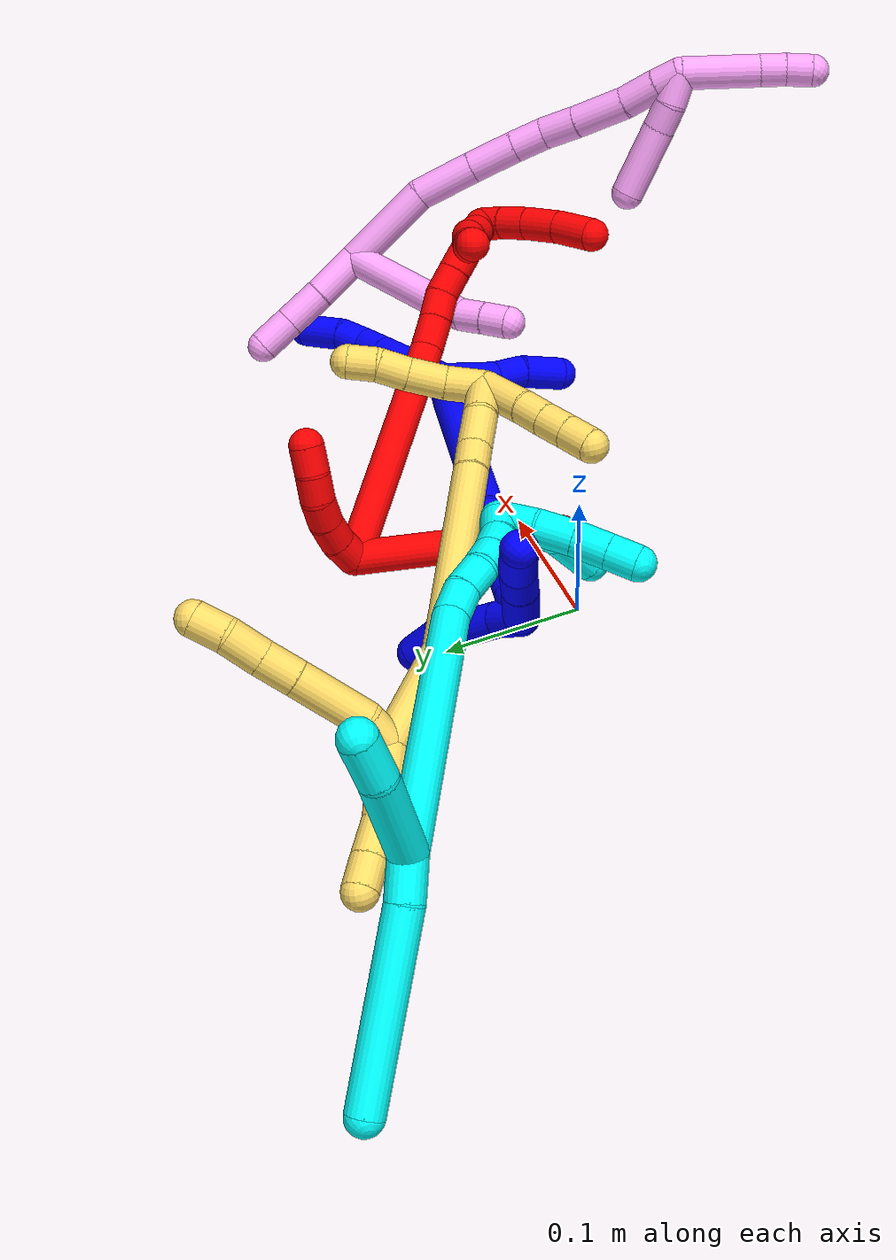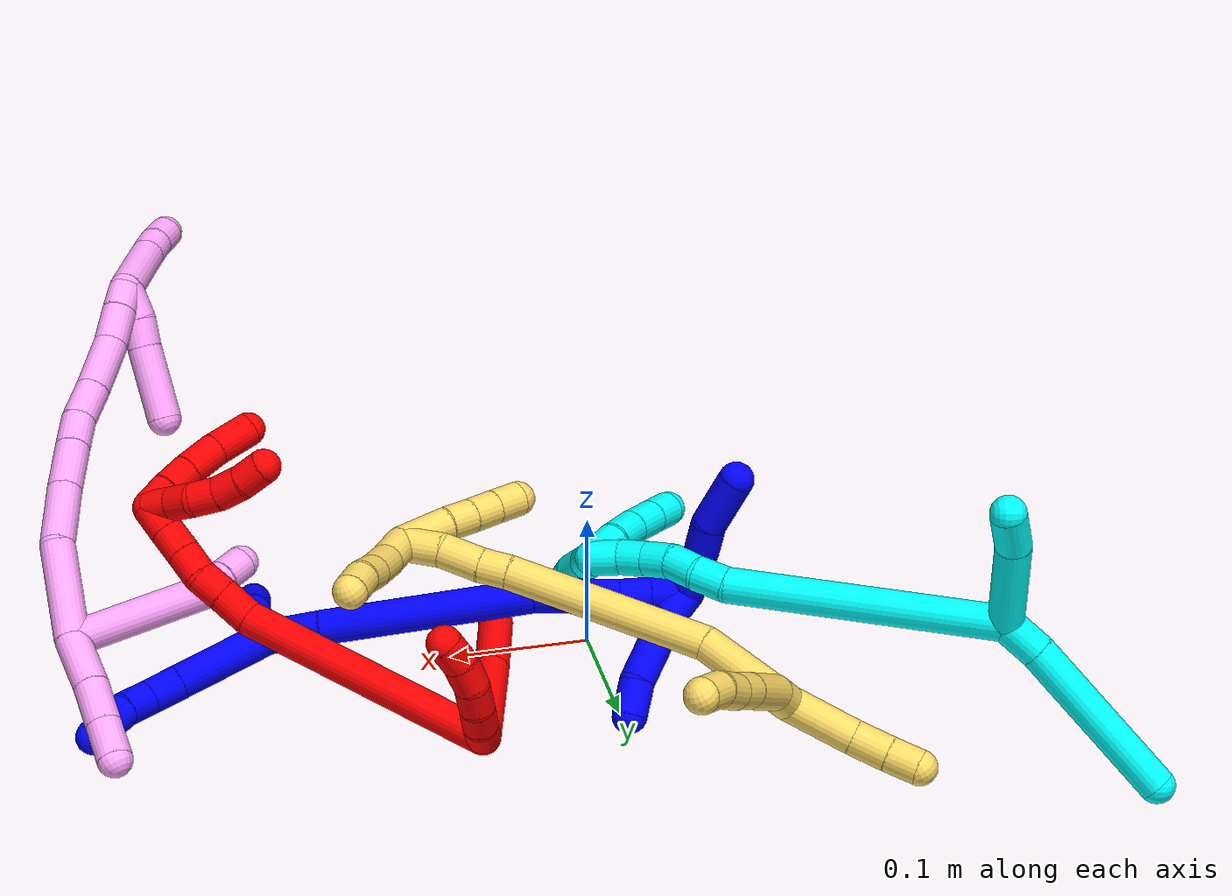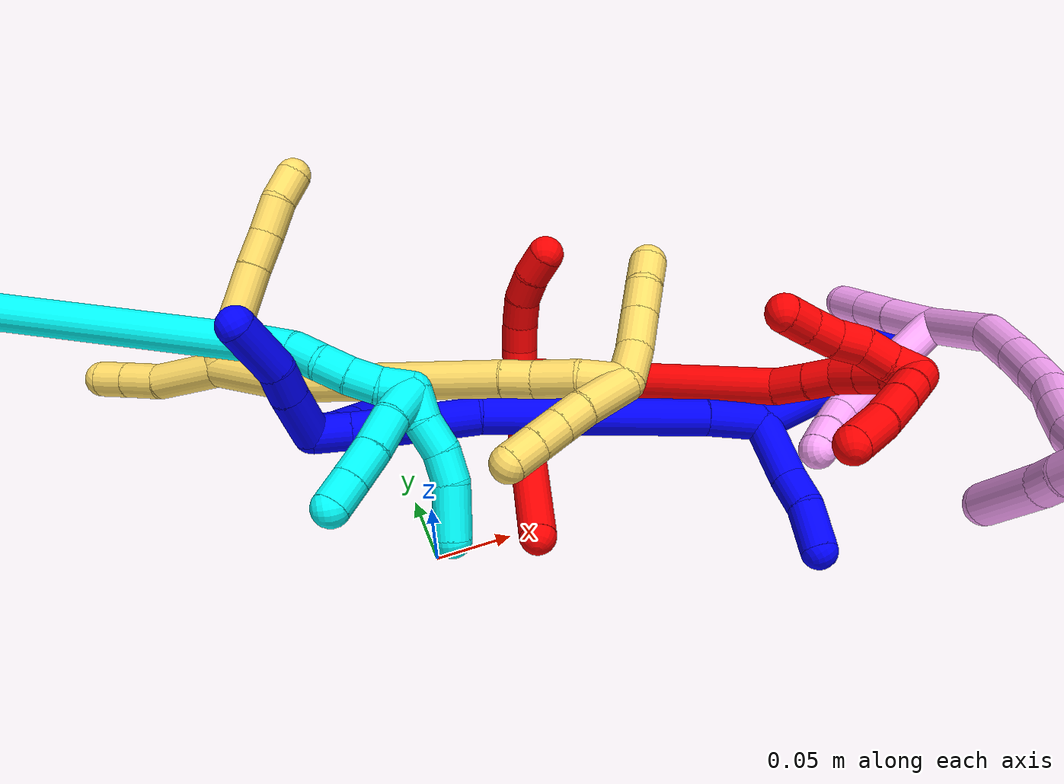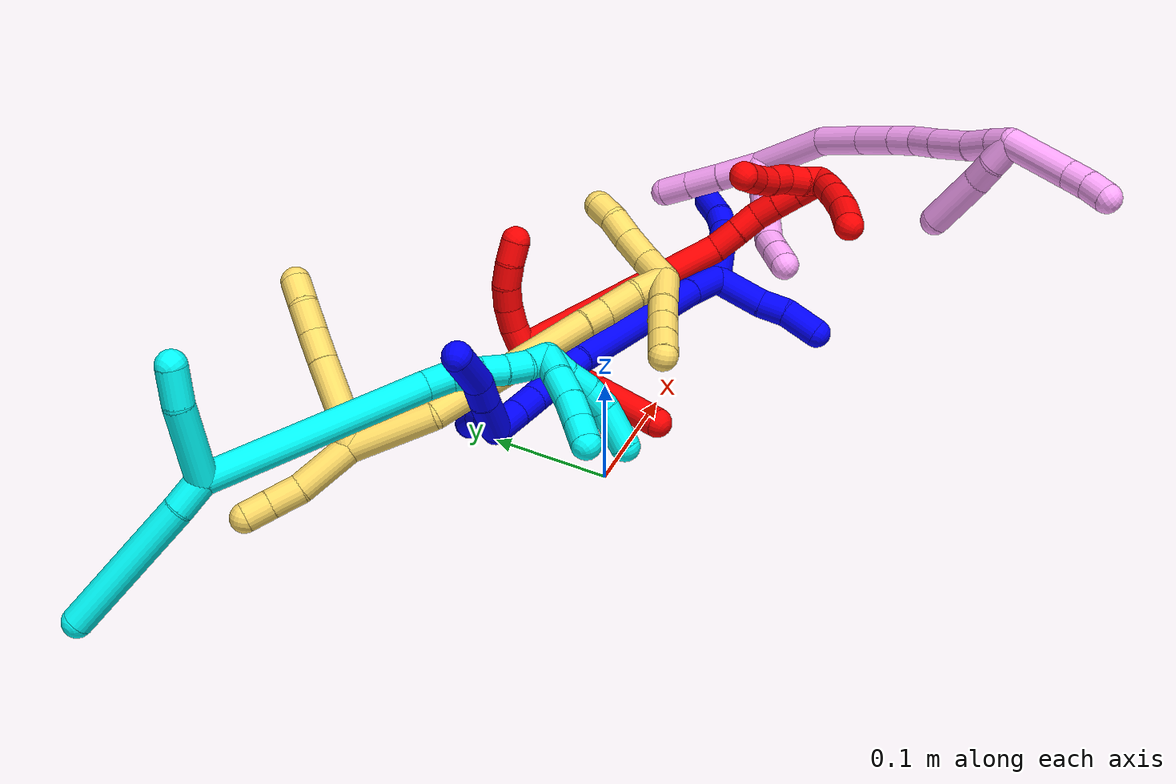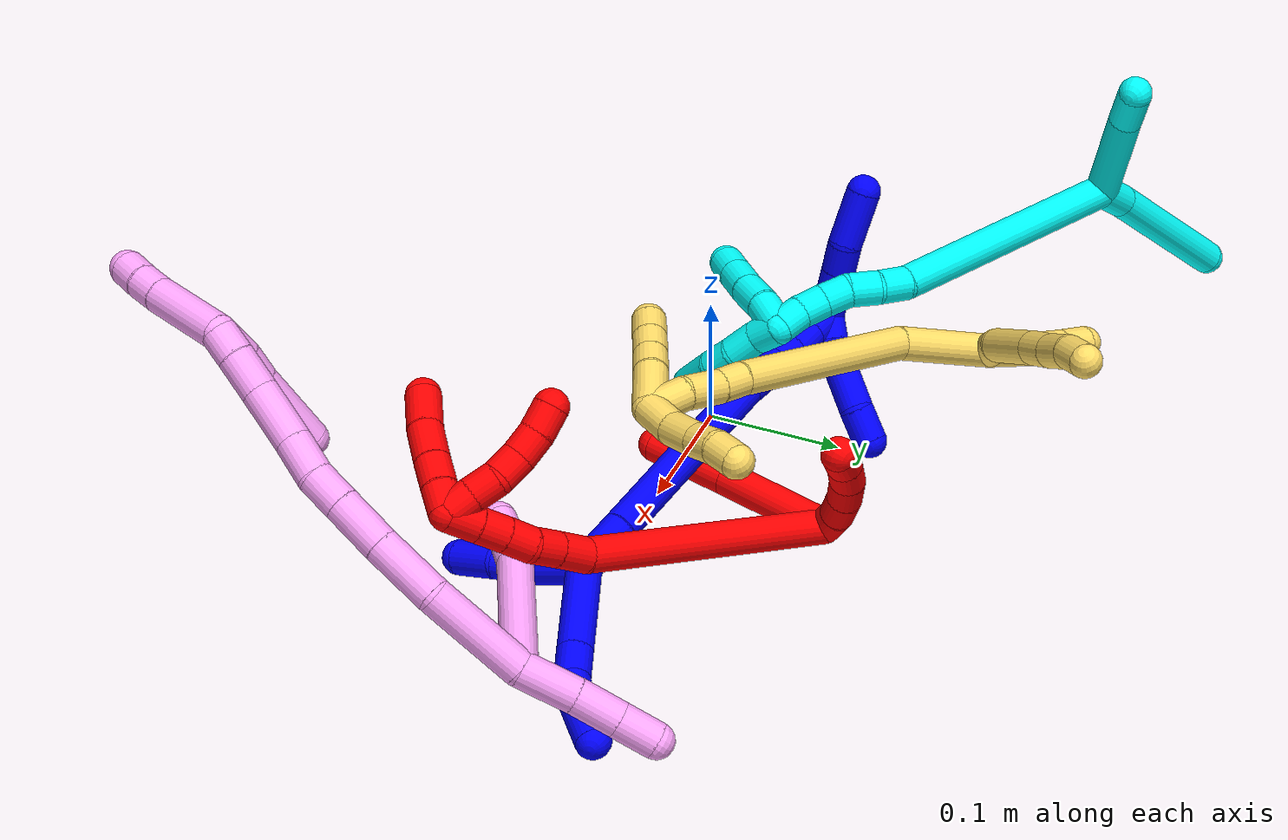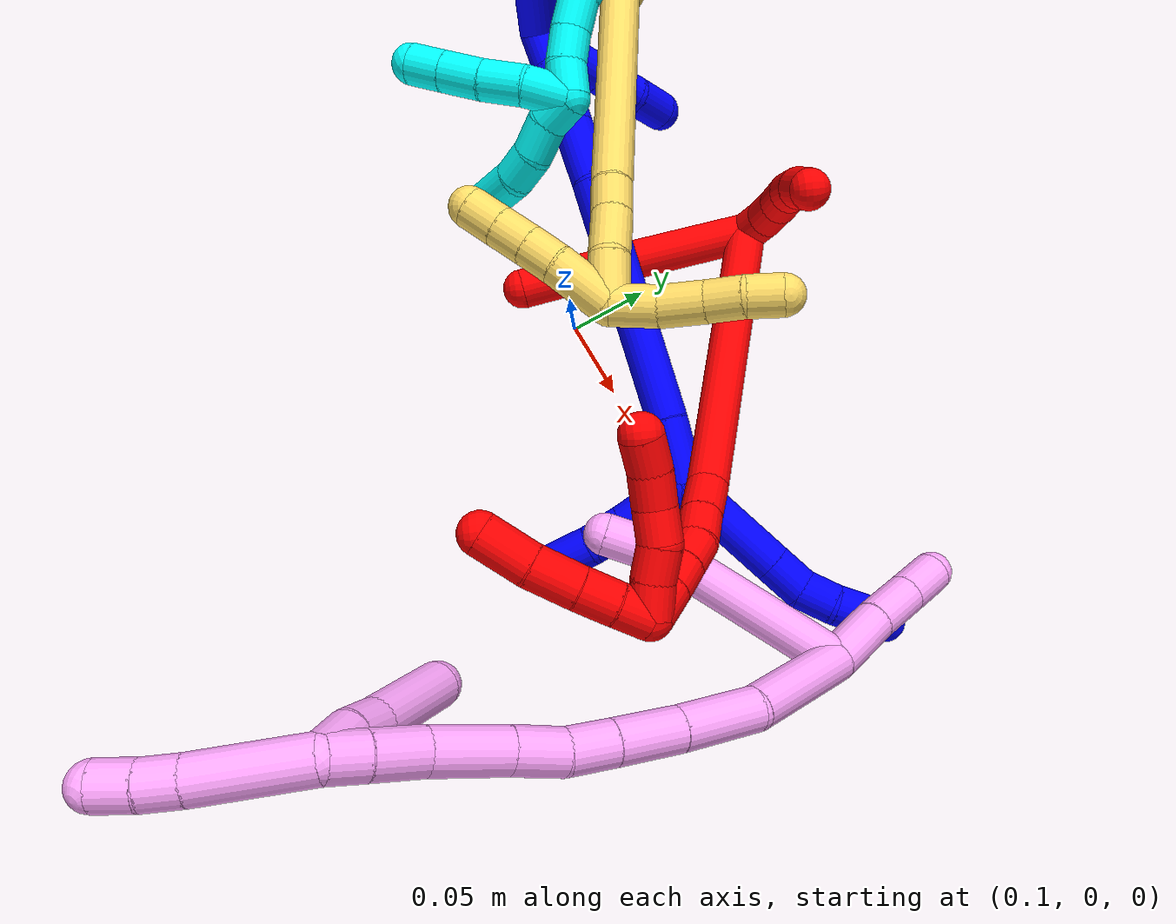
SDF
<sdf version="1.7">
 <world name="default">
  <plugin name="TubeGeneratorPlugin" filename="libtube_generator_plugin.so"/>
  <model name="photoneo_s_sensor">
   <static>1</static>
   <pose>0 0 2 1.57079 1.57079 3.14159</pose>
   <link name="link">
    <inertial><mass>0.1</mass></inertial>
    <sensor name="sensor" type="depth">
     <update_rate>30</update_rate>
     <camera>
      <horizontal_fov>1.22</horizontal_fov>
      <image><width>1920</width><height>1200</height><format>B8G8R8</format></image>
      <clip><near>0.1</near><far>4</far></clip>
      <depth_camera><output>points</output></depth_camera>
     </camera>
     <plugin name="camera_plugin" filename="libgazebo_ros_depth_camera.so">
      <baseline>0.2</baseline>
      <alwaysOn>1</alwaysOn>
      <updateRate>0.0</updateRate>
      <cameraName>camera_ir</cameraName>
      <imageTopicName>/camera/color/image_raw</imageTopicName>
      <cameraInfoTopicName>/camera/color/camera_info</cameraInfoTopicName>
      <depthImageTopicName>/camera/depth/image_raw</depthImageTopicName>
      <depthImageCameraInfoTopicName>/camera/depth/camera_info</depthImageCameraInfoTopicName>
      <pointCloudTopicName>/camera/depth/points</pointCloudTopicName>
      <frameName>fr_optical</frameName>
      <pointCloudCutoff>0.1</pointCloudCutoff>
      <pointCloudCutoffMax>2.0</pointCloudCutoffMax>
      <distortionK1>0</distortionK1>
      <distortionK2>0</distortionK2>
      <distortionK3>0</distortionK3>
      <distortionT1>0</distortionT1>
      <distortionT2>0</distortionT2>
      <CxPrime>0</CxPrime>
      <Cx>0</Cx>
      <Cy>0</Cy>
      <focalLength>0</focalLength>
      <hackBaseline>0</hackBaseline>
     </plugin>
    </sensor>
   </link>
  </model>
  <gravity>0 0 -9.8</gravity>
  <magnetic_field>6e-06 2.3e-05 -4.2e-05</magnetic_field>
  <atmosphere type="adiabatic"/>
  <physics name="default_physics" default="0" type="ode">
   <max_step_size>0.003</max_step_size>
   <real_time_factor>1</real_time_factor>
   <real_time_update_rate>1000</real_time_update_rate>
   <max_contacts>10000</max_contacts>
   <ode>
    <solver>
     <type>quick</type>
     <iters>100</iters>
     <sor>1.3</sor>
     <use_dynamic_moi_rescaling>0</use_dynamic_moi_rescaling>
    </solver>
    <constraints>
     <contact_max_correcting_vel>0</contact_max_correcting_vel>
     <contact_surface_layer>0.001</contact_surface_layer>
     <cfm>0</cfm>
     <erp>0.2</erp>
    </constraints>
   </ode>
  </physics>
  <scene><ambient>0.4 0.4 0.4 1</ambient><background>0.7 0.7 0.7 1</background><shadows>0</shadows></scene>
  <audio><device>default</device></audio>
  <spherical_coordinates>
   <surface_model>EARTH_WGS84</surface_model>
   <latitude_deg>0</latitude_deg>
   <longitude_deg>0</longitude_deg>
   <elevation>0</elevation>
   <heading_deg>0</heading_deg>
  </spherical_coordinates>
  <model name="bin">
   <static>1</static>
   <link name="bottom">
    <collision name="collision-bottom">
     <pose>0 0 -0.01 0 -0 0</pose>
     <geometry><box><size>0.8 0.6 0.02</size></box></geometry>
     <surface>
      <friction><ode><mu>100</mu><mu2>100</mu2></ode></friction>
      <contact><collide_bitmask>65535</collide_bitmask></contact>
     </surface>
    </collision>
   </link>
   <link name="west_wall">
    <collision name="collision-west_wall">
     <pose>-0.41 0 0.1 0 -0 0</pose>
     <geometry><box><size>0.02 0.6 0.2</size></box></geometry>
     <surface>
      <friction><ode><mu>100</mu><mu2>100</mu2></ode></friction>
      <contact><collide_bitmask>65535</collide_bitmask></contact>
     </surface>
    </collision>
   </link>
   <link name="east_wall">
    <collision name="collision-east_wall">
     <pose>0.41 0 0.1 0 -0 0</pose>
     <geometry><box><size>0.02 0.6 0.2</size></box></geometry>
     <surface>
      <friction><ode><mu>100</mu><mu2>100</mu2></ode></friction>
      <contact><collide_bitmask>65535</collide_bitmask></contact>
     </surface>
    </collision>
   </link>
   <link name="south_wall">
    <collision name="collision-south_wall">
     <pose>0 -0.31 0.1 0 -0 0</pose>
     <geometry><box><size>0.8 0.02 0.2</size></box></geometry>
     <surface>
      <friction><ode><mu>100</mu><mu2>100</mu2></ode></friction>
      <contact><collide_bitmask>65535</collide_bitmask></contact>
     </surface>
    </collision>
   </link>
   <link name="north_wall">
    <collision name="collision-north_wall">
     <pose>0 0.31 0.1 0 -0 0</pose>
     <geometry><box><size>0.8 0.02 0.2</size></box></geometry>
     <surface>
      <friction><ode><mu>100</mu><mu2>100</mu2></ode></friction>
      <contact><collide_bitmask>65535</collide_bitmask></contact>
     </surface>
    </collision>
   </link>
  </model>
  <model name="1">
   <static>0</static>
   <link name="1">
    <collision name="collision-cylinder-e_1_2_8">
     <pose>0.003365 0.011829 0.033653 -0.338014 0.094055 -0.016061</pose>
     <geometry><cylinder><radius>0.0125</radius><length>0.071661</length></cylinder></geometry>
     <surface>
      <friction><ode><mu>1.16</mu><mu2>1.16</mu2><slip1>0</slip1><slip2>0</slip2></ode></friction>
      <contact><ode><kp>1e+06</kp><kd>1</kd><max_vel>0</max_vel><min_depth>0.001</min_depth></ode></contact>
     </surface>
    </collision>
    <visual name="visual-cylinder-e_1_2_8">
     <pose>0.003365 0.011829 0.033653 -0.338014 0.094055 -0.016061</pose>
     <geometry><cylinder><radius>0.0125</radius><length>0.071661</length></cylinder></geometry>
     <material><ambient>0 0 1 1</ambient></material>
    </visual>
    <collision name="collision-cylinder-e_2_8_9">
     <pose>0.007819 0.027612 0.07856 -0.33788 0.091065 -0.015543</pose>
     <geometry><cylinder><radius>0.0125</radius><length>0.023954</length></cylinder></geometry>
     <surface>
      <friction><ode><mu>1.16</mu><mu2>1.16</mu2><slip1>0</slip1><slip2>0</slip2></ode></friction>
      <contact><ode><kp>1e+06</kp><kd>1</kd><max_vel>0</max_vel><min_depth>0.001</min_depth></ode></contact>
     </surface>
    </collision>
    <visual name="visual-cylinder-e_2_8_9">
     <pose>0.007819 0.027612 0.07856 -0.33788 0.091065 -0.015543</pose>
     <geometry><cylinder><radius>0.0125</radius><length>0.023954</length></cylinder></geometry>
     <material><ambient>0 0 1 1</ambient></material>
    </visual>
    <collision name="collision-cylinder-e_3_9_10">
     <pose>0.006326 0.03483 0.099982 -0.310576 -0.237222 0.037307</pose>
     <geometry><cylinder><radius>0.0125</radius><length>0.021975</length></cylinder></geometry>
     <surface>
      <friction><ode><mu>1.16</mu><mu2>1.16</mu2><slip1>0</slip1><slip2>0</slip2></ode></friction>
      <contact><ode><kp>1e+06</kp><kd>1</kd><max_vel>0</max_vel><min_depth>0.001</min_depth></ode></contact>
     </surface>
    </collision>
    <visual name="visual-cylinder-e_3_9_10">
     <pose>0.006326 0.03483 0.099982 -0.310576 -0.237222 0.037307</pose>
     <geometry><cylinder><radius>0.0125</radius><length>0.021975</length></cylinder></geometry>
     <material><ambient>0 0 1 1</ambient></material>
    </visual>
    <collision name="collision-cylinder-e_4_10_6">
     <pose>-0.00022 0.0464 0.123489 -0.55698 -0.247157 0.070999</pose>
     <geometry><cylinder><radius>0.0125</radius><length>0.03241</length></cylinder></geometry>
     <surface>
      <friction><ode><mu>1.16</mu><mu2>1.16</mu2><slip1>0</slip1><slip2>0</slip2></ode></friction>
      <contact><ode><kp>1e+06</kp><kd>1</kd><max_vel>0</max_vel><min_depth>0.001</min_depth></ode></contact>
     </surface>
    </collision>
    <visual name="visual-cylinder-e_4_10_6">
     <pose>-0.00022 0.0464 0.123489 -0.55698 -0.247157 0.070999</pose>
     <geometry><cylinder><radius>0.0125</radius><length>0.03241</length></cylinder></geometry>
     <material><ambient>0 0 1 1</ambient></material>
    </visual>
    <collision name="collision-cylinder-e_1_2_11">
     <pose>0.020463 -0.007019 -0.005024 2.19204 1.1716 1.82338</pose>
     <geometry><cylinder><radius>0.0125</radius><length>0.044418</length></cylinder></geometry>
     <surface>
      <friction><ode><mu>1.16</mu><mu2>1.16</mu2><slip1>0</slip1><slip2>0</slip2></ode></friction>
      <contact><ode><kp>1e+06</kp><kd>1</kd><max_vel>0</max_vel><min_depth>0.001</min_depth></ode></contact>
     </surface>
    </collision>
    <visual name="visual-cylinder-e_1_2_11">
     <pose>0.020463 -0.007019 -0.005024 2.19204 1.1716 1.82338</pose>
     <geometry><cylinder><radius>0.0125</radius><length>0.044418</length></cylinder></geometry>
     <material><ambient>0 0 1 1</ambient></material>
    </visual>
    <collision name="collision-cylinder-e_2_11_12">
     <pose>0.050826 -0.02006 -0.012391 1.94177 0.992629 1.33932</pose>
     <geometry><cylinder><radius>0.0125</radius><length>0.023645</length></cylinder></geometry>
     <surface>
      <friction><ode><mu>1.16</mu><mu2>1.16</mu2><slip1>0</slip1><slip2>0</slip2></ode></friction>
      <contact><ode><kp>1e+06</kp><kd>1</kd><max_vel>0</max_vel><min_depth>0.001</min_depth></ode></contact>
     </surface>
    </collision>
    <visual name="visual-cylinder-e_2_11_12">
     <pose>0.050826 -0.02006 -0.012391 1.94177 0.992629 1.33932</pose>
     <geometry><cylinder><radius>0.0125</radius><length>0.023645</length></cylinder></geometry>
     <material><ambient>0 0 1 1</ambient></material>
    </visual>
    <collision name="collision-cylinder-e_3_12_5">
     <pose>0.074709 -0.031135 -0.02056 2.42712 1.06668 2.01409</pose>
     <geometry><cylinder><radius>0.0125</radius><length>0.031938</length></cylinder></geometry>
     <surface>
      <friction><ode><mu>1.16</mu><mu2>1.16</mu2><slip1>0</slip1><slip2>0</slip2></ode></friction>
      <contact><ode><kp>1e+06</kp><kd>1</kd><max_vel>0</max_vel><min_depth>0.001</min_depth></ode></contact>
     </surface>
    </collision>
    <visual name="visual-cylinder-e_3_12_5">
     <pose>0.074709 -0.031135 -0.02056 2.42712 1.06668 2.01409</pose>
     <geometry><cylinder><radius>0.0125</radius><length>0.031938</length></cylinder></geometry>
     <material><ambient>0 0 1 1</ambient></material>
    </visual>
    <collision name="collision-cylinder-e_1_2_13">
     <pose>-0.011257 -0.000228 -0.016506 3.12779 -0.598518 -3.09687</pose>
     <geometry><cylinder><radius>0.0125</radius><length>0.039961</length></cylinder></geometry>
     <surface>
      <friction><ode><mu>1.16</mu><mu2>1.16</mu2><slip1>0</slip1><slip2>0</slip2></ode></friction>
      <contact><ode><kp>1e+06</kp><kd>1</kd><max_vel>0</max_vel><min_depth>0.001</min_depth></ode></contact>
     </surface>
    </collision>
    <visual name="visual-cylinder-e_1_2_13">
     <pose>-0.011257 -0.000228 -0.016506 3.12779 -0.598518 -3.09687</pose>
     <geometry><cylinder><radius>0.0125</radius><length>0.039961</length></cylinder></geometry>
     <material><ambient>0 0 1 1</ambient></material>
    </visual>
    <collision name="collision-cylinder-e_2_13_14">
     <pose>-0.061002 0.000345 -0.098603 -3.12939 -0.530601 3.09667</pose>
     <geometry><cylinder><radius>0.0125</radius><length>0.152107</length></cylinder></geometry>
     <surface>
      <friction><ode><mu>1.16</mu><mu2>1.16</mu2><slip1>0</slip1><slip2>0</slip2></ode></friction>
      <contact><ode><kp>1e+06</kp><kd>1</kd><max_vel>0</max_vel><min_depth>0.001</min_depth></ode></contact>
     </surface>
    </collision>
    <visual name="visual-cylinder-e_2_13_14">
     <pose>-0.061002 0.000345 -0.098603 -3.12939 -0.530601 3.09667</pose>
     <geometry><cylinder><radius>0.0125</radius><length>0.152107</length></cylinder></geometry>
     <material><ambient>0 0 1 1</ambient></material>
    </visual>
    <collision name="collision-cylinder-e_3_14_15">
     <pose>-0.107397 0.004405 -0.182123 -2.96179 -0.409466 2.32243</pose>
     <geometry><cylinder><radius>0.0125</radius><length>0.039729</length></cylinder></geometry>
     <surface>
      <friction><ode><mu>1.16</mu><mu2>1.16</mu2><slip1>0</slip1><slip2>0</slip2></ode></friction>
      <contact><ode><kp>1e+06</kp><kd>1</kd><max_vel>0</max_vel><min_depth>0.001</min_depth></ode></contact>
     </surface>
    </collision>
    <visual name="visual-cylinder-e_3_14_15">
     <pose>-0.107397 0.004405 -0.182123 -2.96179 -0.409466 2.32243</pose>
     <geometry><cylinder><radius>0.0125</radius><length>0.039729</length></cylinder></geometry>
     <material><ambient>0 0 1 1</ambient></material>
    </visual>
    <collision name="collision-cylinder-e_4_15_16">
     <pose>-0.119459 0.009373 -0.209297 -2.95879 -0.415932 2.32206</pose>
     <geometry><cylinder><radius>0.0125</radius><length>0.020557</length></cylinder></geometry>
     <surface>
      <friction><ode><mu>1.16</mu><mu2>1.16</mu2><slip1>0</slip1><slip2>0</slip2></ode></friction>
      <contact><ode><kp>1e+06</kp><kd>1</kd><max_vel>0</max_vel><min_depth>0.001</min_depth></ode></contact>
     </surface>
    </collision>
    <visual name="visual-cylinder-e_4_15_16">
     <pose>-0.119459 0.009373 -0.209297 -2.95879 -0.415932 2.32206</pose>
     <geometry><cylinder><radius>0.0125</radius><length>0.020557</length></cylinder></geometry>
     <material><ambient>0 0 1 1</ambient></material>
    </visual>
    <collision name="collision-cylinder-e_5_16_17">
     <pose>-0.128344 0.012133 -0.228705 -3.03851 -0.433825 2.68173</pose>
     <geometry><cylinder><radius>0.0125</radius><length>0.022518</length></cylinder></geometry>
     <surface>
      <friction><ode><mu>1.16</mu><mu2>1.16</mu2><slip1>0</slip1><slip2>0</slip2></ode></friction>
      <contact><ode><kp>1e+06</kp><kd>1</kd><max_vel>0</max_vel><min_depth>0.001</min_depth></ode></contact>
     </surface>
    </collision>
    <visual name="visual-cylinder-e_5_16_17">
     <pose>-0.128344 0.012133 -0.228705 -3.03851 -0.433825 2.68173</pose>
     <geometry><cylinder><radius>0.0125</radius><length>0.022518</length></cylinder></geometry>
     <material><ambient>0 0 1 1</ambient></material>
    </visual>
    <collision name="collision-cylinder-e_6_17_1">
     <pose>-0.138408 0.014227 -0.250196 -3.04982 -0.438218 2.73486</pose>
     <geometry><cylinder><radius>0.0125</radius><length>0.025127</length></cylinder></geometry>
     <surface>
      <friction><ode><mu>1.16</mu><mu2>1.16</mu2><slip1>0</slip1><slip2>0</slip2></ode></friction>
      <contact><ode><kp>1e+06</kp><kd>1</kd><max_vel>0</max_vel><min_depth>0.001</min_depth></ode></contact>
     </surface>
    </collision>
    <visual name="visual-cylinder-e_6_17_1">
     <pose>-0.138408 0.014227 -0.250196 -3.04982 -0.438218 2.73486</pose>
     <geometry><cylinder><radius>0.0125</radius><length>0.025127</length></cylinder></geometry>
     <material><ambient>0 0 1 1</ambient></material>
    </visual>
    <collision name="collision-cylinder-e_1_1_18">
     <pose>-0.156903 0.002189 -0.263067 1.68823 -0.785128 -0.871791</pose>
     <geometry><cylinder><radius>0.0125</radius><length>0.037243</length></cylinder></geometry>
     <surface>
      <friction><ode><mu>1.16</mu><mu2>1.16</mu2><slip1>0</slip1><slip2>0</slip2></ode></friction>
      <contact><ode><kp>1e+06</kp><kd>1</kd><max_vel>0</max_vel><min_depth>0.001</min_depth></ode></contact>
     </surface>
    </collision>
    <visual name="visual-cylinder-e_1_1_18">
     <pose>-0.156903 0.002189 -0.263067 1.68823 -0.785128 -0.871791</pose>
     <geometry><cylinder><radius>0.0125</radius><length>0.037243</length></cylinder></geometry>
     <material><ambient>0 0 1 1</ambient></material>
    </visual>
    <collision name="collision-cylinder-e_2_18_19">
     <pose>-0.177873 -0.018659 -0.264742 1.58774 -0.787768 -0.799851</pose>
     <geometry><cylinder><radius>0.0125</radius><length>0.022025</length></cylinder></geometry>
     <surface>
      <friction><ode><mu>1.16</mu><mu2>1.16</mu2><slip1>0</slip1><slip2>0</slip2></ode></friction>
      <contact><ode><kp>1e+06</kp><kd>1</kd><max_vel>0</max_vel><min_depth>0.001</min_depth></ode></contact>
     </surface>
    </collision>
    <visual name="visual-cylinder-e_2_18_19">
     <pose>-0.177873 -0.018659 -0.264742 1.58774 -0.787768 -0.799851</pose>
     <geometry><cylinder><radius>0.0125</radius><length>0.022025</length></cylinder></geometry>
     <material><ambient>0 0 1 1</ambient></material>
    </visual>
    <collision name="collision-cylinder-e_3_19_4">
     <pose>-0.200799 -0.039005 -0.270158 1.96851 -0.836702 -1.17925</pose>
     <geometry><cylinder><radius>0.0125</radius><length>0.040732</length></cylinder></geometry>
     <surface>
      <friction><ode><mu>1.16</mu><mu2>1.16</mu2><slip1>0</slip1><slip2>0</slip2></ode></friction>
      <contact><ode><kp>1e+06</kp><kd>1</kd><max_vel>0</max_vel><min_depth>0.001</min_depth></ode></contact>
     </surface>
    </collision>
    <visual name="visual-cylinder-e_3_19_4">
     <pose>-0.200799 -0.039005 -0.270158 1.96851 -0.836702 -1.17925</pose>
     <geometry><cylinder><radius>0.0125</radius><length>0.040732</length></cylinder></geometry>
     <material><ambient>0 0 1 1</ambient></material>
    </visual>
    <collision name="collision-cylinder-e_1_1_20">
     <pose>-0.142122 0.022889 -0.253479 -0.758218 0.144955 -0.057833</pose>
     <geometry><cylinder><radius>0.0125</radius><length>0.022397</length></cylinder></geometry>
     <surface>
      <friction><ode><mu>1.16</mu><mu2>1.16</mu2><slip1>0</slip1><slip2>0</slip2></ode></friction>
      <contact><ode><kp>1e+06</kp><kd>1</kd><max_vel>0</max_vel><min_depth>0.001</min_depth></ode></contact>
     </surface>
    </collision>
    <visual name="visual-cylinder-e_1_1_20">
     <pose>-0.142122 0.022889 -0.253479 -0.758218 0.144955 -0.057833</pose>
     <geometry><cylinder><radius>0.0125</radius><length>0.022397</length></cylinder></geometry>
     <material><ambient>0 0 1 1</ambient></material>
    </visual>
    <collision name="collision-cylinder-e_2_20_21">
     <pose>-0.140434 0.039611 -0.238547 -0.923122 0.006128 -0.003048</pose>
     <geometry><cylinder><radius>0.0125</radius><length>0.022829</length></cylinder></geometry>
     <surface>
      <friction><ode><mu>1.16</mu><mu2>1.16</mu2><slip1>0</slip1><slip2>0</slip2></ode></friction>
      <contact><ode><kp>1e+06</kp><kd>1</kd><max_vel>0</max_vel><min_depth>0.001</min_depth></ode></contact>
     </surface>
    </collision>
    <visual name="visual-cylinder-e_2_20_21">
     <pose>-0.140434 0.039611 -0.238547 -0.923122 0.006128 -0.003048</pose>
     <geometry><cylinder><radius>0.0125</radius><length>0.022829</length></cylinder></geometry>
     <material><ambient>0 0 1 1</ambient></material>
    </visual>
    <collision name="collision-cylinder-e_3_21_22">
     <pose>-0.140328 0.060628 -0.222751 -0.928718 0.002473 -0.001239</pose>
     <geometry><cylinder><radius>0.0125</radius><length>0.029754</length></cylinder></geometry>
     <surface>
      <friction><ode><mu>1.16</mu><mu2>1.16</mu2><slip1>0</slip1><slip2>0</slip2></ode></friction>
      <contact><ode><kp>1e+06</kp><kd>1</kd><max_vel>0</max_vel><min_depth>0.001</min_depth></ode></contact>
     </surface>
    </collision>
    <visual name="visual-cylinder-e_3_21_22">
     <pose>-0.140328 0.060628 -0.222751 -0.928718 0.002473 -0.001239</pose>
     <geometry><cylinder><radius>0.0125</radius><length>0.029754</length></cylinder></geometry>
     <material><ambient>0 0 1 1</ambient></material>
    </visual>
    <collision name="collision-cylinder-e_4_22_3">
     <pose>-0.139424 0.084162 -0.209288 -1.19727 0.069347 -0.047314</pose>
     <geometry><cylinder><radius>0.0125</radius><length>0.025021</length></cylinder></geometry>
     <surface>
      <friction><ode><mu>1.16</mu><mu2>1.16</mu2><slip1>0</slip1><slip2>0</slip2></ode></friction>
      <contact><ode><kp>1e+06</kp><kd>1</kd><max_vel>0</max_vel><min_depth>0.001</min_depth></ode></contact>
     </surface>
    </collision>
    <visual name="visual-cylinder-e_4_22_3">
     <pose>-0.139424 0.084162 -0.209288 -1.19727 0.069347 -0.047314</pose>
     <geometry><cylinder><radius>0.0125</radius><length>0.025021</length></cylinder></geometry>
     <material><ambient>0 0 1 1</ambient></material>
    </visual>
    <collision name="collision-sphere-3">
     <pose>-0.138557 0.095782 -0.204734 0 -0 0</pose>
     <geometry><sphere><radius>0.0125</radius></sphere></geometry>
     <surface>
      <friction><ode><mu>1.16</mu><mu2>1.16</mu2><slip1>0</slip1><slip2>0</slip2></ode></friction>
      <contact><ode><kp>1e+06</kp><kd>1</kd><max_vel>0</max_vel><min_depth>0.001</min_depth></ode></contact>
     </surface>
    </collision>
    <visual name="visual-sphere-3">
     <pose>-0.138557 0.095782 -0.204734 0 -0 0</pose>
     <geometry><sphere><radius>0.0125</radius></sphere></geometry>
     <material><ambient>0 0 1 1</ambient></material>
    </visual>
    <collision name="collision-sphere-22">
     <pose>-0.140291 0.072542 -0.213842 0 -0 0</pose>
     <geometry><sphere><radius>0.0125</radius></sphere></geometry>
     <surface>
      <friction><ode><mu>1.16</mu><mu2>1.16</mu2><slip1>0</slip1><slip2>0</slip2></ode></friction>
      <contact><ode><kp>1e+06</kp><kd>1</kd><max_vel>0</max_vel><min_depth>0.001</min_depth></ode></contact>
     </surface>
    </collision>
    <visual name="visual-sphere-22">
     <pose>-0.140291 0.072542 -0.213842 0 -0 0</pose>
     <geometry><sphere><radius>0.0125</radius></sphere></geometry>
     <material><ambient>0 0 1 1</ambient></material>
    </visual>
    <collision name="collision-sphere-21">
     <pose>-0.140364 0.048714 -0.23166 0 -0 0</pose>
     <geometry><sphere><radius>0.0125</radius></sphere></geometry>
     <surface>
      <friction><ode><mu>1.16</mu><mu2>1.16</mu2><slip1>0</slip1><slip2>0</slip2></ode></friction>
      <contact><ode><kp>1e+06</kp><kd>1</kd><max_vel>0</max_vel><min_depth>0.001</min_depth></ode></contact>
     </surface>
    </collision>
    <visual name="visual-sphere-21">
     <pose>-0.140364 0.048714 -0.23166 0 -0 0</pose>
     <geometry><sphere><radius>0.0125</radius></sphere></geometry>
     <material><ambient>0 0 1 1</ambient></material>
    </visual>
    <collision name="collision-sphere-20">
     <pose>-0.140504 0.030508 -0.245433 0 -0 0</pose>
     <geometry><sphere><radius>0.0125</radius></sphere></geometry>
     <surface>
      <friction><ode><mu>1.16</mu><mu2>1.16</mu2><slip1>0</slip1><slip2>0</slip2></ode></friction>
      <contact><ode><kp>1e+06</kp><kd>1</kd><max_vel>0</max_vel><min_depth>0.001</min_depth></ode></contact>
     </surface>
    </collision>
    <visual name="visual-sphere-20">
     <pose>-0.140504 0.030508 -0.245433 0 -0 0</pose>
     <geometry><sphere><radius>0.0125</radius></sphere></geometry>
     <material><ambient>0 0 1 1</ambient></material>
    </visual>
    <collision name="collision-sphere-4">
     <pose>-0.215919 -0.051583 -0.275442 0 -0 0</pose>
     <geometry><sphere><radius>0.0125</radius></sphere></geometry>
     <surface>
      <friction><ode><mu>1.16</mu><mu2>1.16</mu2><slip1>0</slip1><slip2>0</slip2></ode></friction>
      <contact><ode><kp>1e+06</kp><kd>1</kd><max_vel>0</max_vel><min_depth>0.001</min_depth></ode></contact>
     </surface>
    </collision>
    <visual name="visual-sphere-4">
     <pose>-0.215919 -0.051583 -0.275442 0 -0 0</pose>
     <geometry><sphere><radius>0.0125</radius></sphere></geometry>
     <material><ambient>0 0 1 1</ambient></material>
    </visual>
    <collision name="collision-sphere-11">
     <pose>0.040925 -0.014038 -0.010049 0 -0 0</pose>
     <geometry><sphere><radius>0.0125</radius></sphere></geometry>
     <surface>
      <friction><ode><mu>1.16</mu><mu2>1.16</mu2><slip1>0</slip1><slip2>0</slip2></ode></friction>
      <contact><ode><kp>1e+06</kp><kd>1</kd><max_vel>0</max_vel><min_depth>0.001</min_depth></ode></contact>
     </surface>
    </collision>
    <visual name="visual-sphere-11">
     <pose>0.040925 -0.014038 -0.010049 0 -0 0</pose>
     <geometry><sphere><radius>0.0125</radius></sphere></geometry>
     <material><ambient>0 0 1 1</ambient></material>
    </visual>
    <collision name="collision-sphere-6">
     <pose>-0.004185 0.054706 0.136826 0 -0 0</pose>
     <geometry><sphere><radius>0.0125</radius></sphere></geometry>
     <surface>
      <friction><ode><mu>1.16</mu><mu2>1.16</mu2><slip1>0</slip1><slip2>0</slip2></ode></friction>
      <contact><ode><kp>1e+06</kp><kd>1</kd><max_vel>0</max_vel><min_depth>0.001</min_depth></ode></contact>
     </surface>
    </collision>
    <visual name="visual-sphere-6">
     <pose>-0.004185 0.054706 0.136826 0 -0 0</pose>
     <geometry><sphere><radius>0.0125</radius></sphere></geometry>
     <material><ambient>0 0 1 1</ambient></material>
    </visual>
    <collision name="collision-sphere-10">
     <pose>0.003744 0.038094 0.110151 0 -0 0</pose>
     <geometry><sphere><radius>0.0125</radius></sphere></geometry>
     <surface>
      <friction><ode><mu>1.16</mu><mu2>1.16</mu2><slip1>0</slip1><slip2>0</slip2></ode></friction>
      <contact><ode><kp>1e+06</kp><kd>1</kd><max_vel>0</max_vel><min_depth>0.001</min_depth></ode></contact>
     </surface>
    </collision>
    <visual name="visual-sphere-10">
     <pose>0.003744 0.038094 0.110151 0 -0 0</pose>
     <geometry><sphere><radius>0.0125</radius></sphere></geometry>
     <material><ambient>0 0 1 1</ambient></material>
    </visual>
    <collision name="collision-sphere-9">
     <pose>0.008908 0.031566 0.089813 0 -0 0</pose>
     <geometry><sphere><radius>0.0125</radius></sphere></geometry>
     <surface>
      <friction><ode><mu>1.16</mu><mu2>1.16</mu2><slip1>0</slip1><slip2>0</slip2></ode></friction>
      <contact><ode><kp>1e+06</kp><kd>1</kd><max_vel>0</max_vel><min_depth>0.001</min_depth></ode></contact>
     </surface>
    </collision>
    <visual name="visual-sphere-9">
     <pose>0.008908 0.031566 0.089813 0 -0 0</pose>
     <geometry><sphere><radius>0.0125</radius></sphere></geometry>
     <material><ambient>0 0 1 1</ambient></material>
    </visual>
    <collision name="collision-sphere-2">
     <geometry><sphere><radius>0.0125</radius></sphere></geometry>
     <surface>
      <friction><ode><mu>1.16</mu><mu2>1.16</mu2><slip1>0</slip1><slip2>0</slip2></ode></friction>
      <contact><ode><kp>1e+06</kp><kd>1</kd><max_vel>0</max_vel><min_depth>0.001</min_depth></ode></contact>
     </surface>
    </collision>
    <visual name="visual-sphere-2">
     <geometry><sphere><radius>0.0125</radius></sphere></geometry>
     <material><ambient>0 0 1 1</ambient></material>
    </visual>
    <collision name="collision-sphere-19">
     <pose>-0.185678 -0.026426 -0.264874 0 -0 0</pose>
     <geometry><sphere><radius>0.0125</radius></sphere></geometry>
     <surface>
      <friction><ode><mu>1.16</mu><mu2>1.16</mu2><slip1>0</slip1><slip2>0</slip2></ode></friction>
      <contact><ode><kp>1e+06</kp><kd>1</kd><max_vel>0</max_vel><min_depth>0.001</min_depth></ode></contact>
     </surface>
    </collision>
    <visual name="visual-sphere-19">
     <pose>-0.185678 -0.026426 -0.264874 0 -0 0</pose>
     <geometry><sphere><radius>0.0125</radius></sphere></geometry>
     <material><ambient>0 0 1 1</ambient></material>
    </visual>
    <collision name="collision-sphere-8">
     <pose>0.00673 0.023659 0.067307 0 -0 0</pose>
     <geometry><sphere><radius>0.0125</radius></sphere></geometry>
     <surface>
      <friction><ode><mu>1.16</mu><mu2>1.16</mu2><slip1>0</slip1><slip2>0</slip2></ode></friction>
      <contact><ode><kp>1e+06</kp><kd>1</kd><max_vel>0</max_vel><min_depth>0.001</min_depth></ode></contact>
     </surface>
    </collision>
    <visual name="visual-sphere-8">
     <pose>0.00673 0.023659 0.067307 0 -0 0</pose>
     <geometry><sphere><radius>0.0125</radius></sphere></geometry>
     <material><ambient>0 0 1 1</ambient></material>
    </visual>
    <collision name="collision-sphere-12">
     <pose>0.060727 -0.026081 -0.014733 0 -0 0</pose>
     <geometry><sphere><radius>0.0125</radius></sphere></geometry>
     <surface>
      <friction><ode><mu>1.16</mu><mu2>1.16</mu2><slip1>0</slip1><slip2>0</slip2></ode></friction>
      <contact><ode><kp>1e+06</kp><kd>1</kd><max_vel>0</max_vel><min_depth>0.001</min_depth></ode></contact>
     </surface>
    </collision>
    <visual name="visual-sphere-12">
     <pose>0.060727 -0.026081 -0.014733 0 -0 0</pose>
     <geometry><sphere><radius>0.0125</radius></sphere></geometry>
     <material><ambient>0 0 1 1</ambient></material>
    </visual>
    <collision name="collision-sphere-5">
     <pose>0.088691 -0.036189 -0.026387 0 -0 0</pose>
     <geometry><sphere><radius>0.0125</radius></sphere></geometry>
     <surface>
      <friction><ode><mu>1.16</mu><mu2>1.16</mu2><slip1>0</slip1><slip2>0</slip2></ode></friction>
      <contact><ode><kp>1e+06</kp><kd>1</kd><max_vel>0</max_vel><min_depth>0.001</min_depth></ode></contact>
     </surface>
    </collision>
    <visual name="visual-sphere-5">
     <pose>0.088691 -0.036189 -0.026387 0 -0 0</pose>
     <geometry><sphere><radius>0.0125</radius></sphere></geometry>
     <material><ambient>0 0 1 1</ambient></material>
    </visual>
    <collision name="collision-sphere-13">
     <pose>-0.022515 -0.000456 -0.033012 0 -0 0</pose>
     <geometry><sphere><radius>0.0125</radius></sphere></geometry>
     <surface>
      <friction><ode><mu>1.16</mu><mu2>1.16</mu2><slip1>0</slip1><slip2>0</slip2></ode></friction>
      <contact><ode><kp>1e+06</kp><kd>1</kd><max_vel>0</max_vel><min_depth>0.001</min_depth></ode></contact>
     </surface>
    </collision>
    <visual name="visual-sphere-13">
     <pose>-0.022515 -0.000456 -0.033012 0 -0 0</pose>
     <geometry><sphere><radius>0.0125</radius></sphere></geometry>
     <material><ambient>0 0 1 1</ambient></material>
    </visual>
    <collision name="collision-sphere-14">
     <pose>-0.099489 0.001146 -0.164194 0 -0 0</pose>
     <geometry><sphere><radius>0.0125</radius></sphere></geometry>
     <surface>
      <friction><ode><mu>1.16</mu><mu2>1.16</mu2><slip1>0</slip1><slip2>0</slip2></ode></friction>
      <contact><ode><kp>1e+06</kp><kd>1</kd><max_vel>0</max_vel><min_depth>0.001</min_depth></ode></contact>
     </surface>
    </collision>
    <visual name="visual-sphere-14">
     <pose>-0.099489 0.001146 -0.164194 0 -0 0</pose>
     <geometry><sphere><radius>0.0125</radius></sphere></geometry>
     <material><ambient>0 0 1 1</ambient></material>
    </visual>
    <collision name="collision-sphere-15">
     <pose>-0.115306 0.007663 -0.200052 0 -0 0</pose>
     <geometry><sphere><radius>0.0125</radius></sphere></geometry>
     <surface>
      <friction><ode><mu>1.16</mu><mu2>1.16</mu2><slip1>0</slip1><slip2>0</slip2></ode></friction>
      <contact><ode><kp>1e+06</kp><kd>1</kd><max_vel>0</max_vel><min_depth>0.001</min_depth></ode></contact>
     </surface>
    </collision>
    <visual name="visual-sphere-15">
     <pose>-0.115306 0.007663 -0.200052 0 -0 0</pose>
     <geometry><sphere><radius>0.0125</radius></sphere></geometry>
     <material><ambient>0 0 1 1</ambient></material>
    </visual>
    <collision name="collision-sphere-16">
     <pose>-0.123612 0.011082 -0.218543 0 -0 0</pose>
     <geometry><sphere><radius>0.0125</radius></sphere></geometry>
     <surface>
      <friction><ode><mu>1.16</mu><mu2>1.16</mu2><slip1>0</slip1><slip2>0</slip2></ode></friction>
      <contact><ode><kp>1e+06</kp><kd>1</kd><max_vel>0</max_vel><min_depth>0.001</min_depth></ode></contact>
     </surface>
    </collision>
    <visual name="visual-sphere-16">
     <pose>-0.123612 0.011082 -0.218543 0 -0 0</pose>
     <geometry><sphere><radius>0.0125</radius></sphere></geometry>
     <material><ambient>0 0 1 1</ambient></material>
    </visual>
    <collision name="collision-sphere-17">
     <pose>-0.133077 0.013184 -0.238867 0 -0 0</pose>
     <geometry><sphere><radius>0.0125</radius></sphere></geometry>
     <surface>
      <friction><ode><mu>1.16</mu><mu2>1.16</mu2><slip1>0</slip1><slip2>0</slip2></ode></friction>
      <contact><ode><kp>1e+06</kp><kd>1</kd><max_vel>0</max_vel><min_depth>0.001</min_depth></ode></contact>
     </surface>
    </collision>
    <visual name="visual-sphere-17">
     <pose>-0.133077 0.013184 -0.238867 0 -0 0</pose>
     <geometry><sphere><radius>0.0125</radius></sphere></geometry>
     <material><ambient>0 0 1 1</ambient></material>
    </visual>
    <collision name="collision-sphere-1">
     <pose>-0.143739 0.01527 -0.261524 0 -0 0</pose>
     <geometry><sphere><radius>0.0125</radius></sphere></geometry>
     <surface>
      <friction><ode><mu>1.16</mu><mu2>1.16</mu2><slip1>0</slip1><slip2>0</slip2></ode></friction>
      <contact><ode><kp>1e+06</kp><kd>1</kd><max_vel>0</max_vel><min_depth>0.001</min_depth></ode></contact>
     </surface>
    </collision>
    <visual name="visual-sphere-1">
     <pose>-0.143739 0.01527 -0.261524 0 -0 0</pose>
     <geometry><sphere><radius>0.0125</radius></sphere></geometry>
     <material><ambient>0 0 1 1</ambient></material>
    </visual>
    <collision name="collision-sphere-18">
     <pose>-0.170067 -0.010891 -0.264611 0 -0 0</pose>
     <geometry><sphere><radius>0.0125</radius></sphere></geometry>
     <surface>
      <friction><ode><mu>1.16</mu><mu2>1.16</mu2><slip1>0</slip1><slip2>0</slip2></ode></friction>
      <contact><ode><kp>1e+06</kp><kd>1</kd><max_vel>0</max_vel><min_depth>0.001</min_depth></ode></contact>
     </surface>
    </collision>
    <visual name="visual-sphere-18">
     <pose>-0.170067 -0.010891 -0.264611 0 -0 0</pose>
     <geometry><sphere><radius>0.0125</radius></sphere></geometry>
     <material><ambient>0 0 1 1</ambient></material>
    </visual>
    <inertial>
     <pose>-0.06634 0.008598 -0.105243 0 -0 0</pose>
     <mass>0.75</mass>
     <inertia>
      <ixx>-0.000212</ixx>
      <ixy>0</ixy>
      <ixz>0</ixz>
      <iyy>0.000399</iyy>
      <iyz>0</iyz>
      <izz>0.000135</izz>
     </inertia>
    </inertial>
   </link>
   <pose>0.23283 0.00317 0.036109 -1.41551 0.607424 -1.26375</pose>
  </model>
  <model name="2">
   <static>0</static>
   <link name="2">
    <collision name="collision-cylinder-e_1_2_8">
     <pose>0.002323 -0.005637 -0.042913 3.01099 0.053624 0.778376</pose>
     <geometry><cylinder><radius>0.0125</radius><length>0.086689</length></cylinder></geometry>
     <surface>
      <friction><ode><mu>1.16</mu><mu2>1.16</mu2><slip1>0</slip1><slip2>0</slip2></ode></friction>
      <contact><ode><kp>1e+06</kp><kd>1</kd><max_vel>0</max_vel><min_depth>0.001</min_depth></ode></contact>
     </surface>
    </collision>
    <visual name="visual-cylinder-e_1_2_8">
     <pose>0.002323 -0.005637 -0.042913 3.01099 0.053624 0.778376</pose>
     <geometry><cylinder><radius>0.0125</radius><length>0.086689</length></cylinder></geometry>
     <material><ambient>1 0 0 1</ambient></material>
    </visual>
    <collision name="collision-cylinder-e_2_8_6">
     <pose>0.0066 -0.016002 -0.117066 2.99138 0.061759 0.779049</pose>
     <geometry><cylinder><radius>0.0125</radius><length>0.063311</length></cylinder></geometry>
     <surface>
      <friction><ode><mu>1.16</mu><mu2>1.16</mu2><slip1>0</slip1><slip2>0</slip2></ode></friction>
      <contact><ode><kp>1e+06</kp><kd>1</kd><max_vel>0</max_vel><min_depth>0.001</min_depth></ode></contact>
     </surface>
    </collision>
    <visual name="visual-cylinder-e_2_8_6">
     <pose>0.0066 -0.016002 -0.117066 2.99138 0.061759 0.779049</pose>
     <geometry><cylinder><radius>0.0125</radius><length>0.063311</length></cylinder></geometry>
     <material><ambient>1 0 0 1</ambient></material>
    </visual>
    <collision name="collision-cylinder-e_1_2_9">
     <pose>-0.007569 -0.003587 0.005464 0.580896 -0.858487 -0.271929</pose>
     <geometry><cylinder><radius>0.0125</radius><length>0.02</length></cylinder></geometry>
     <surface>
      <friction><ode><mu>1.16</mu><mu2>1.16</mu2><slip1>0</slip1><slip2>0</slip2></ode></friction>
      <contact><ode><kp>1e+06</kp><kd>1</kd><max_vel>0</max_vel><min_depth>0.001</min_depth></ode></contact>
     </surface>
    </collision>
    <visual name="visual-cylinder-e_1_2_9">
     <pose>-0.007569 -0.003587 0.005464 0.580896 -0.858487 -0.271929</pose>
     <geometry><cylinder><radius>0.0125</radius><length>0.02</length></cylinder></geometry>
     <material><ambient>1 0 0 1</ambient></material>
    </visual>
    <collision name="collision-cylinder-e_2_9_10">
     <pose>-0.023281 -0.01168 0.014585 0.889102 -0.951596 -0.481394</pose>
     <geometry><cylinder><radius>0.0125</radius><length>0.02</length></cylinder></geometry>
     <surface>
      <friction><ode><mu>1.16</mu><mu2>1.16</mu2><slip1>0</slip1><slip2>0</slip2></ode></friction>
      <contact><ode><kp>1e+06</kp><kd>1</kd><max_vel>0</max_vel><min_depth>0.001</min_depth></ode></contact>
     </surface>
    </collision>
    <visual name="visual-cylinder-e_2_9_10">
     <pose>-0.023281 -0.01168 0.014585 0.889102 -0.951596 -0.481394</pose>
     <geometry><cylinder><radius>0.0125</radius><length>0.02</length></cylinder></geometry>
     <material><ambient>1 0 0 1</ambient></material>
    </visual>
    <collision name="collision-cylinder-e_3_10_11">
     <pose>-0.039526 -0.021614 0.020454 1.18366 -0.944588 -0.661571</pose>
     <geometry><cylinder><radius>0.0125</radius><length>0.02</length></cylinder></geometry>
     <surface>
      <friction><ode><mu>1.16</mu><mu2>1.16</mu2><slip1>0</slip1><slip2>0</slip2></ode></friction>
      <contact><ode><kp>1e+06</kp><kd>1</kd><max_vel>0</max_vel><min_depth>0.001</min_depth></ode></contact>
     </surface>
    </collision>
    <visual name="visual-cylinder-e_3_10_11">
     <pose>-0.039526 -0.021614 0.020454 1.18366 -0.944588 -0.661571</pose>
     <geometry><cylinder><radius>0.0125</radius><length>0.02</length></cylinder></geometry>
     <material><ambient>1 0 0 1</ambient></material>
    </visual>
    <collision name="collision-cylinder-e_4_11_12">
     <pose>-0.054323 -0.034342 0.024043 1.38449 -0.733364 -0.616544</pose>
     <geometry><cylinder><radius>0.0125</radius><length>0.02</length></cylinder></geometry>
     <surface>
      <friction><ode><mu>1.16</mu><mu2>1.16</mu2><slip1>0</slip1><slip2>0</slip2></ode></friction>
      <contact><ode><kp>1e+06</kp><kd>1</kd><max_vel>0</max_vel><min_depth>0.001</min_depth></ode></contact>
     </surface>
    </collision>
    <visual name="visual-cylinder-e_4_11_12">
     <pose>-0.054323 -0.034342 0.024043 1.38449 -0.733364 -0.616544</pose>
     <geometry><cylinder><radius>0.0125</radius><length>0.02</length></cylinder></geometry>
     <material><ambient>1 0 0 1</ambient></material>
    </visual>
    <collision name="collision-cylinder-e_5_12_5">
     <pose>-0.066207 -0.049999 0.027215 1.35907 -0.54572 -0.444686</pose>
     <geometry><cylinder><radius>0.0125</radius><length>0.02</length></cylinder></geometry>
     <surface>
      <friction><ode><mu>1.16</mu><mu2>1.16</mu2><slip1>0</slip1><slip2>0</slip2></ode></friction>
      <contact><ode><kp>1e+06</kp><kd>1</kd><max_vel>0</max_vel><min_depth>0.001</min_depth></ode></contact>
     </surface>
    </collision>
    <visual name="visual-cylinder-e_5_12_5">
     <pose>-0.066207 -0.049999 0.027215 1.35907 -0.54572 -0.444686</pose>
     <geometry><cylinder><radius>0.0125</radius><length>0.02</length></cylinder></geometry>
     <material><ambient>1 0 0 1</ambient></material>
    </visual>
    <collision name="collision-cylinder-e_1_2_13">
     <pose>0.020305 -0.089548 -0.025084 1.84392 0.214969 0.282661</pose>
     <geometry><cylinder><radius>0.0125</radius><length>0.190371</length></cylinder></geometry>
     <surface>
      <friction><ode><mu>1.16</mu><mu2>1.16</mu2><slip1>0</slip1><slip2>0</slip2></ode></friction>
      <contact><ode><kp>1e+06</kp><kd>1</kd><max_vel>0</max_vel><min_depth>0.001</min_depth></ode></contact>
     </surface>
    </collision>
    <visual name="visual-cylinder-e_1_2_13">
     <pose>0.020305 -0.089548 -0.025084 1.84392 0.214969 0.282661</pose>
     <geometry><cylinder><radius>0.0125</radius><length>0.190371</length></cylinder></geometry>
     <material><ambient>1 0 0 1</ambient></material>
    </visual>
    <collision name="collision-cylinder-e_2_13_14">
     <pose>0.039569 -0.19111 -0.053585 1.84789 -0.083117 -0.110004</pose>
     <geometry><cylinder><radius>0.0125</radius><length>0.025068</length></cylinder></geometry>
     <surface>
      <friction><ode><mu>1.16</mu><mu2>1.16</mu2><slip1>0</slip1><slip2>0</slip2></ode></friction>
      <contact><ode><kp>1e+06</kp><kd>1</kd><max_vel>0</max_vel><min_depth>0.001</min_depth></ode></contact>
     </surface>
    </collision>
    <visual name="visual-cylinder-e_2_13_14">
     <pose>0.039569 -0.19111 -0.053585 1.84789 -0.083117 -0.110004</pose>
     <geometry><cylinder><radius>0.0125</radius><length>0.025068</length></cylinder></geometry>
     <material><ambient>1 0 0 1</ambient></material>
    </visual>
    <collision name="collision-cylinder-e_3_14_15">
     <pose>0.037742 -0.213318 -0.059432 1.80481 -0.074906 -0.094834</pose>
     <geometry><cylinder><radius>0.0125</radius><length>0.021017</length></cylinder></geometry>
     <surface>
      <friction><ode><mu>1.16</mu><mu2>1.16</mu2><slip1>0</slip1><slip2>0</slip2></ode></friction>
      <contact><ode><kp>1e+06</kp><kd>1</kd><max_vel>0</max_vel><min_depth>0.001</min_depth></ode></contact>
     </surface>
    </collision>
    <visual name="visual-cylinder-e_3_14_15">
     <pose>0.037742 -0.213318 -0.059432 1.80481 -0.074906 -0.094834</pose>
     <geometry><cylinder><radius>0.0125</radius><length>0.021017</length></cylinder></geometry>
     <material><ambient>1 0 0 1</ambient></material>
    </visual>
    <collision name="collision-cylinder-e_4_15_16">
     <pose>0.035256 -0.232335 -0.066758 2.07736 -0.166848 -0.282159</pose>
     <geometry><cylinder><radius>0.0125</radius><length>0.020465</length></cylinder></geometry>
     <surface>
      <friction><ode><mu>1.16</mu><mu2>1.16</mu2><slip1>0</slip1><slip2>0</slip2></ode></friction>
      <contact><ode><kp>1e+06</kp><kd>1</kd><max_vel>0</max_vel><min_depth>0.001</min_depth></ode></contact>
     </surface>
    </collision>
    <visual name="visual-cylinder-e_4_15_16">
     <pose>0.035256 -0.232335 -0.066758 2.07736 -0.166848 -0.282159</pose>
     <geometry><cylinder><radius>0.0125</radius><length>0.020465</length></cylinder></geometry>
     <material><ambient>1 0 0 1</ambient></material>
    </visual>
    <collision name="collision-cylinder-e_5_16_17">
     <pose>0.032134 -0.249922 -0.076551 2.08042 -0.14074 -0.239133</pose>
     <geometry><cylinder><radius>0.0125</radius><length>0.02028</length></cylinder></geometry>
     <surface>
      <friction><ode><mu>1.16</mu><mu2>1.16</mu2><slip1>0</slip1><slip2>0</slip2></ode></friction>
      <contact><ode><kp>1e+06</kp><kd>1</kd><max_vel>0</max_vel><min_depth>0.001</min_depth></ode></contact>
     </surface>
    </collision>
    <visual name="visual-cylinder-e_5_16_17">
     <pose>0.032134 -0.249922 -0.076551 2.08042 -0.14074 -0.239133</pose>
     <geometry><cylinder><radius>0.0125</radius><length>0.02028</length></cylinder></geometry>
     <material><ambient>1 0 0 1</ambient></material>
    </visual>
    <collision name="collision-cylinder-e_6_17_1">
     <pose>0.029121 -0.268382 -0.087228 2.10823 -0.140055 -0.245664</pose>
     <geometry><cylinder><radius>0.0125</radius><length>0.022798</length></cylinder></geometry>
     <surface>
      <friction><ode><mu>1.16</mu><mu2>1.16</mu2><slip1>0</slip1><slip2>0</slip2></ode></friction>
      <contact><ode><kp>1e+06</kp><kd>1</kd><max_vel>0</max_vel><min_depth>0.001</min_depth></ode></contact>
     </surface>
    </collision>
    <visual name="visual-cylinder-e_6_17_1">
     <pose>0.029121 -0.268382 -0.087228 2.10823 -0.140055 -0.245664</pose>
     <geometry><cylinder><radius>0.0125</radius><length>0.022798</length></cylinder></geometry>
     <material><ambient>1 0 0 1</ambient></material>
    </visual>
    <collision name="collision-cylinder-e_1_1_18">
     <pose>0.020195 -0.271524 -0.091204 -1.30252 -0.823402 0.64257</pose>
     <geometry><cylinder><radius>0.0125</radius><length>0.02</length></cylinder></geometry>
     <surface>
      <friction><ode><mu>1.16</mu><mu2>1.16</mu2><slip1>0</slip1><slip2>0</slip2></ode></friction>
      <contact><ode><kp>1e+06</kp><kd>1</kd><max_vel>0</max_vel><min_depth>0.001</min_depth></ode></contact>
     </surface>
    </collision>
    <visual name="visual-cylinder-e_1_1_18">
     <pose>0.020195 -0.271524 -0.091204 -1.30252 -0.823402 0.64257</pose>
     <geometry><cylinder><radius>0.0125</radius><length>0.02</length></cylinder></geometry>
     <material><ambient>1 0 0 1</ambient></material>
    </visual>
    <collision name="collision-cylinder-e_2_18_19">
     <pose>0.005314 -0.259129 -0.086411 -1.09749 -0.85502 0.543327</pose>
     <geometry><cylinder><radius>0.0125</radius><length>0.02</length></cylinder></geometry>
     <surface>
      <friction><ode><mu>1.16</mu><mu2>1.16</mu2><slip1>0</slip1><slip2>0</slip2></ode></friction>
      <contact><ode><kp>1e+06</kp><kd>1</kd><max_vel>0</max_vel><min_depth>0.001</min_depth></ode></contact>
     </surface>
    </collision>
    <visual name="visual-cylinder-e_2_18_19">
     <pose>0.005314 -0.259129 -0.086411 -1.09749 -0.85502 0.543327</pose>
     <geometry><cylinder><radius>0.0125</radius><length>0.02</length></cylinder></geometry>
     <material><ambient>1 0 0 1</ambient></material>
    </visual>
    <collision name="collision-cylinder-e_3_19_20">
     <pose>-0.009496 -0.246423 -0.083717 -1.61398 -0.813103 0.844945</pose>
     <geometry><cylinder><radius>0.0125</radius><length>0.02</length></cylinder></geometry>
     <surface>
      <friction><ode><mu>1.16</mu><mu2>1.16</mu2><slip1>0</slip1><slip2>0</slip2></ode></friction>
      <contact><ode><kp>1e+06</kp><kd>1</kd><max_vel>0</max_vel><min_depth>0.001</min_depth></ode></contact>
     </surface>
    </collision>
    <visual name="visual-cylinder-e_3_19_20">
     <pose>-0.009496 -0.246423 -0.083717 -1.61398 -0.813103 0.844945</pose>
     <geometry><cylinder><radius>0.0125</radius><length>0.02</length></cylinder></geometry>
     <material><ambient>1 0 0 1</ambient></material>
    </visual>
    <collision name="collision-cylinder-e_4_20_21">
     <pose>-0.025347 -0.234434 -0.084191 -1.60537 -1.03264 1.06259</pose>
     <geometry><cylinder><radius>0.0125</radius><length>0.02</length></cylinder></geometry>
     <surface>
      <friction><ode><mu>1.16</mu><mu2>1.16</mu2><slip1>0</slip1><slip2>0</slip2></ode></friction>
      <contact><ode><kp>1e+06</kp><kd>1</kd><max_vel>0</max_vel><min_depth>0.001</min_depth></ode></contact>
     </surface>
    </collision>
    <visual name="visual-cylinder-e_4_20_21">
     <pose>-0.025347 -0.234434 -0.084191 -1.60537 -1.03264 1.06259</pose>
     <geometry><cylinder><radius>0.0125</radius><length>0.02</length></cylinder></geometry>
     <material><ambient>1 0 0 1</ambient></material>
    </visual>
    <collision name="collision-cylinder-e_5_21_4">
     <pose>-0.043026 -0.225349 -0.085642 -1.88198 -1.14146 1.44431</pose>
     <geometry><cylinder><radius>0.0125</radius><length>0.02</length></cylinder></geometry>
     <surface>
      <friction><ode><mu>1.16</mu><mu2>1.16</mu2><slip1>0</slip1><slip2>0</slip2></ode></friction>
      <contact><ode><kp>1e+06</kp><kd>1</kd><max_vel>0</max_vel><min_depth>0.001</min_depth></ode></contact>
     </surface>
    </collision>
    <visual name="visual-cylinder-e_5_21_4">
     <pose>-0.043026 -0.225349 -0.085642 -1.88198 -1.14146 1.44431</pose>
     <geometry><cylinder><radius>0.0125</radius><length>0.02</length></cylinder></geometry>
     <material><ambient>1 0 0 1</ambient></material>
    </visual>
    <collision name="collision-cylinder-e_1_1_22">
     <pose>0.022486 -0.276021 -0.1014 -2.90127 -0.528288 2.30182</pose>
     <geometry><cylinder><radius>0.0125</radius><length>0.020012</length></cylinder></geometry>
     <surface>
      <friction><ode><mu>1.16</mu><mu2>1.16</mu2><slip1>0</slip1><slip2>0</slip2></ode></friction>
      <contact><ode><kp>1e+06</kp><kd>1</kd><max_vel>0</max_vel><min_depth>0.001</min_depth></ode></contact>
     </surface>
    </collision>
    <visual name="visual-cylinder-e_1_1_22">
     <pose>0.022486 -0.276021 -0.1014 -2.90127 -0.528288 2.30182</pose>
     <geometry><cylinder><radius>0.0125</radius><length>0.020012</length></cylinder></geometry>
     <material><ambient>1 0 0 1</ambient></material>
    </visual>
    <collision name="collision-cylinder-e_2_22_23">
     <pose>0.012535 -0.270987 -0.119004 -2.8289 -0.469194 1.97548</pose>
     <geometry><cylinder><radius>0.0125</radius><length>0.021706</length></cylinder></geometry>
     <surface>
      <friction><ode><mu>1.16</mu><mu2>1.16</mu2><slip1>0</slip1><slip2>0</slip2></ode></friction>
      <contact><ode><kp>1e+06</kp><kd>1</kd><max_vel>0</max_vel><min_depth>0.001</min_depth></ode></contact>
     </surface>
    </collision>
    <visual name="visual-cylinder-e_2_22_23">
     <pose>0.012535 -0.270987 -0.119004 -2.8289 -0.469194 1.97548</pose>
     <geometry><cylinder><radius>0.0125</radius><length>0.021706</length></cylinder></geometry>
     <material><ambient>1 0 0 1</ambient></material>
    </visual>
    <collision name="collision-cylinder-e_3_23_24">
     <pose>0.001749 -0.263341 -0.139833 -2.75954 -0.438973 1.71317</pose>
     <geometry><cylinder><radius>0.0125</radius><length>0.027665</length></cylinder></geometry>
     <surface>
      <friction><ode><mu>1.16</mu><mu2>1.16</mu2><slip1>0</slip1><slip2>0</slip2></ode></friction>
      <contact><ode><kp>1e+06</kp><kd>1</kd><max_vel>0</max_vel><min_depth>0.001</min_depth></ode></contact>
     </surface>
    </collision>
    <visual name="visual-cylinder-e_3_23_24">
     <pose>0.001749 -0.263341 -0.139833 -2.75954 -0.438973 1.71317</pose>
     <geometry><cylinder><radius>0.0125</radius><length>0.027665</length></cylinder></geometry>
     <material><ambient>1 0 0 1</ambient></material>
    </visual>
    <collision name="collision-cylinder-e_4_24_3">
     <pose>-0.011042 -0.251838 -0.163278 -2.6176 -0.46844 1.45425</pose>
     <geometry><cylinder><radius>0.0125</radius><length>0.030617</length></cylinder></geometry>
     <surface>
      <friction><ode><mu>1.16</mu><mu2>1.16</mu2><slip1>0</slip1><slip2>0</slip2></ode></friction>
      <contact><ode><kp>1e+06</kp><kd>1</kd><max_vel>0</max_vel><min_depth>0.001</min_depth></ode></contact>
     </surface>
    </collision>
    <visual name="visual-cylinder-e_4_24_3">
     <pose>-0.011042 -0.251838 -0.163278 -2.6176 -0.46844 1.45425</pose>
     <geometry><cylinder><radius>0.0125</radius><length>0.030617</length></cylinder></geometry>
     <material><ambient>1 0 0 1</ambient></material>
    </visual>
    <collision name="collision-sphere-3">
     <pose>-0.017954 -0.245004 -0.175104 0 -0 0</pose>
     <geometry><sphere><radius>0.0125</radius></sphere></geometry>
     <surface>
      <friction><ode><mu>1.16</mu><mu2>1.16</mu2><slip1>0</slip1><slip2>0</slip2></ode></friction>
      <contact><ode><kp>1e+06</kp><kd>1</kd><max_vel>0</max_vel><min_depth>0.001</min_depth></ode></contact>
     </surface>
    </collision>
    <visual name="visual-sphere-3">
     <pose>-0.017954 -0.245004 -0.175104 0 -0 0</pose>
     <geometry><sphere><radius>0.0125</radius></sphere></geometry>
     <material><ambient>1 0 0 1</ambient></material>
    </visual>
    <collision name="collision-sphere-24">
     <pose>-0.00413 -0.258673 -0.151451 0 -0 0</pose>
     <geometry><sphere><radius>0.0125</radius></sphere></geometry>
     <surface>
      <friction><ode><mu>1.16</mu><mu2>1.16</mu2><slip1>0</slip1><slip2>0</slip2></ode></friction>
      <contact><ode><kp>1e+06</kp><kd>1</kd><max_vel>0</max_vel><min_depth>0.001</min_depth></ode></contact>
     </surface>
    </collision>
    <visual name="visual-sphere-24">
     <pose>-0.00413 -0.258673 -0.151451 0 -0 0</pose>
     <geometry><sphere><radius>0.0125</radius></sphere></geometry>
     <material><ambient>1 0 0 1</ambient></material>
    </visual>
    <collision name="collision-sphere-23">
     <pose>0.007628 -0.268009 -0.128214 0 -0 0</pose>
     <geometry><sphere><radius>0.0125</radius></sphere></geometry>
     <surface>
      <friction><ode><mu>1.16</mu><mu2>1.16</mu2><slip1>0</slip1><slip2>0</slip2></ode></friction>
      <contact><ode><kp>1e+06</kp><kd>1</kd><max_vel>0</max_vel><min_depth>0.001</min_depth></ode></contact>
     </surface>
    </collision>
    <visual name="visual-sphere-23">
     <pose>0.007628 -0.268009 -0.128214 0 -0 0</pose>
     <geometry><sphere><radius>0.0125</radius></sphere></geometry>
     <material><ambient>1 0 0 1</ambient></material>
    </visual>
    <collision name="collision-sphere-22">
     <pose>0.017442 -0.273964 -0.109793 0 -0 0</pose>
     <geometry><sphere><radius>0.0125</radius></sphere></geometry>
     <surface>
      <friction><ode><mu>1.16</mu><mu2>1.16</mu2><slip1>0</slip1><slip2>0</slip2></ode></friction>
      <contact><ode><kp>1e+06</kp><kd>1</kd><max_vel>0</max_vel><min_depth>0.001</min_depth></ode></contact>
     </surface>
    </collision>
    <visual name="visual-sphere-22">
     <pose>0.017442 -0.273964 -0.109793 0 -0 0</pose>
     <geometry><sphere><radius>0.0125</radius></sphere></geometry>
     <material><ambient>1 0 0 1</ambient></material>
    </visual>
    <collision name="collision-sphere-4">
     <pose>-0.052118 -0.221386 -0.086917 0 -0 0</pose>
     <geometry><sphere><radius>0.0125</radius></sphere></geometry>
     <surface>
      <friction><ode><mu>1.16</mu><mu2>1.16</mu2><slip1>0</slip1><slip2>0</slip2></ode></friction>
      <contact><ode><kp>1e+06</kp><kd>1</kd><max_vel>0</max_vel><min_depth>0.001</min_depth></ode></contact>
     </surface>
    </collision>
    <visual name="visual-sphere-4">
     <pose>-0.052118 -0.221386 -0.086917 0 -0 0</pose>
     <geometry><sphere><radius>0.0125</radius></sphere></geometry>
     <material><ambient>1 0 0 1</ambient></material>
    </visual>
    <collision name="collision-sphere-21">
     <pose>-0.033933 -0.229312 -0.084368 0 -0 0</pose>
     <geometry><sphere><radius>0.0125</radius></sphere></geometry>
     <surface>
      <friction><ode><mu>1.16</mu><mu2>1.16</mu2><slip1>0</slip1><slip2>0</slip2></ode></friction>
      <contact><ode><kp>1e+06</kp><kd>1</kd><max_vel>0</max_vel><min_depth>0.001</min_depth></ode></contact>
     </surface>
    </collision>
    <visual name="visual-sphere-21">
     <pose>-0.033933 -0.229312 -0.084368 0 -0 0</pose>
     <geometry><sphere><radius>0.0125</radius></sphere></geometry>
     <material><ambient>1 0 0 1</ambient></material>
    </visual>
    <collision name="collision-sphere-20">
     <pose>-0.01676 -0.239557 -0.084013 0 -0 0</pose>
     <geometry><sphere><radius>0.0125</radius></sphere></geometry>
     <surface>
      <friction><ode><mu>1.16</mu><mu2>1.16</mu2><slip1>0</slip1><slip2>0</slip2></ode></friction>
      <contact><ode><kp>1e+06</kp><kd>1</kd><max_vel>0</max_vel><min_depth>0.001</min_depth></ode></contact>
     </surface>
    </collision>
    <visual name="visual-sphere-20">
     <pose>-0.01676 -0.239557 -0.084013 0 -0 0</pose>
     <geometry><sphere><radius>0.0125</radius></sphere></geometry>
     <material><ambient>1 0 0 1</ambient></material>
    </visual>
    <collision name="collision-sphere-11">
     <pose>-0.047629 -0.027041 0.022667 0 -0 0</pose>
     <geometry><sphere><radius>0.0125</radius></sphere></geometry>
     <surface>
      <friction><ode><mu>1.16</mu><mu2>1.16</mu2><slip1>0</slip1><slip2>0</slip2></ode></friction>
      <contact><ode><kp>1e+06</kp><kd>1</kd><max_vel>0</max_vel><min_depth>0.001</min_depth></ode></contact>
     </surface>
    </collision>
    <visual name="visual-sphere-11">
     <pose>-0.047629 -0.027041 0.022667 0 -0 0</pose>
     <geometry><sphere><radius>0.0125</radius></sphere></geometry>
     <material><ambient>1 0 0 1</ambient></material>
    </visual>
    <collision name="collision-sphere-10">
     <pose>-0.031424 -0.016187 0.018242 0 -0 0</pose>
     <geometry><sphere><radius>0.0125</radius></sphere></geometry>
     <surface>
      <friction><ode><mu>1.16</mu><mu2>1.16</mu2><slip1>0</slip1><slip2>0</slip2></ode></friction>
      <contact><ode><kp>1e+06</kp><kd>1</kd><max_vel>0</max_vel><min_depth>0.001</min_depth></ode></contact>
     </surface>
    </collision>
    <visual name="visual-sphere-10">
     <pose>-0.031424 -0.016187 0.018242 0 -0 0</pose>
     <geometry><sphere><radius>0.0125</radius></sphere></geometry>
     <material><ambient>1 0 0 1</ambient></material>
    </visual>
    <collision name="collision-sphere-6">
     <pose>0.008554 -0.02073 -0.148306 0 -0 0</pose>
     <geometry><sphere><radius>0.0125</radius></sphere></geometry>
     <surface>
      <friction><ode><mu>1.16</mu><mu2>1.16</mu2><slip1>0</slip1><slip2>0</slip2></ode></friction>
      <contact><ode><kp>1e+06</kp><kd>1</kd><max_vel>0</max_vel><min_depth>0.001</min_depth></ode></contact>
     </surface>
    </collision>
    <visual name="visual-sphere-6">
     <pose>0.008554 -0.02073 -0.148306 0 -0 0</pose>
     <geometry><sphere><radius>0.0125</radius></sphere></geometry>
     <material><ambient>1 0 0 1</ambient></material>
    </visual>
    <collision name="collision-sphere-9">
     <pose>-0.015137 -0.007173 0.010928 0 -0 0</pose>
     <geometry><sphere><radius>0.0125</radius></sphere></geometry>
     <surface>
      <friction><ode><mu>1.16</mu><mu2>1.16</mu2><slip1>0</slip1><slip2>0</slip2></ode></friction>
      <contact><ode><kp>1e+06</kp><kd>1</kd><max_vel>0</max_vel><min_depth>0.001</min_depth></ode></contact>
     </surface>
    </collision>
    <visual name="visual-sphere-9">
     <pose>-0.015137 -0.007173 0.010928 0 -0 0</pose>
     <geometry><sphere><radius>0.0125</radius></sphere></geometry>
     <material><ambient>1 0 0 1</ambient></material>
    </visual>
    <collision name="collision-sphere-2">
     <geometry><sphere><radius>0.0125</radius></sphere></geometry>
     <surface>
      <friction><ode><mu>1.16</mu><mu2>1.16</mu2><slip1>0</slip1><slip2>0</slip2></ode></friction>
      <contact><ode><kp>1e+06</kp><kd>1</kd><max_vel>0</max_vel><min_depth>0.001</min_depth></ode></contact>
     </surface>
    </collision>
    <visual name="visual-sphere-2">
     <geometry><sphere><radius>0.0125</radius></sphere></geometry>
     <material><ambient>1 0 0 1</ambient></material>
    </visual>
    <collision name="collision-sphere-19">
     <pose>-0.002232 -0.253289 -0.08342 0 -0 0</pose>
     <geometry><sphere><radius>0.0125</radius></sphere></geometry>
     <surface>
      <friction><ode><mu>1.16</mu><mu2>1.16</mu2><slip1>0</slip1><slip2>0</slip2></ode></friction>
      <contact><ode><kp>1e+06</kp><kd>1</kd><max_vel>0</max_vel><min_depth>0.001</min_depth></ode></contact>
     </surface>
    </collision>
    <visual name="visual-sphere-19">
     <pose>-0.002232 -0.253289 -0.08342 0 -0 0</pose>
     <geometry><sphere><radius>0.0125</radius></sphere></geometry>
     <material><ambient>1 0 0 1</ambient></material>
    </visual>
    <collision name="collision-sphere-8">
     <pose>0.004646 -0.011273 -0.085827 0 -0 0</pose>
     <geometry><sphere><radius>0.0125</radius></sphere></geometry>
     <surface>
      <friction><ode><mu>1.16</mu><mu2>1.16</mu2><slip1>0</slip1><slip2>0</slip2></ode></friction>
      <contact><ode><kp>1e+06</kp><kd>1</kd><max_vel>0</max_vel><min_depth>0.001</min_depth></ode></contact>
     </surface>
    </collision>
    <visual name="visual-sphere-8">
     <pose>0.004646 -0.011273 -0.085827 0 -0 0</pose>
     <geometry><sphere><radius>0.0125</radius></sphere></geometry>
     <material><ambient>1 0 0 1</ambient></material>
    </visual>
    <collision name="collision-sphere-12">
     <pose>-0.061017 -0.041642 0.025419 0 -0 0</pose>
     <geometry><sphere><radius>0.0125</radius></sphere></geometry>
     <surface>
      <friction><ode><mu>1.16</mu><mu2>1.16</mu2><slip1>0</slip1><slip2>0</slip2></ode></friction>
      <contact><ode><kp>1e+06</kp><kd>1</kd><max_vel>0</max_vel><min_depth>0.001</min_depth></ode></contact>
     </surface>
    </collision>
    <visual name="visual-sphere-12">
     <pose>-0.061017 -0.041642 0.025419 0 -0 0</pose>
     <geometry><sphere><radius>0.0125</radius></sphere></geometry>
     <material><ambient>1 0 0 1</ambient></material>
    </visual>
    <collision name="collision-sphere-5">
     <pose>-0.071397 -0.058356 0.029012 0 -0 0</pose>
     <geometry><sphere><radius>0.0125</radius></sphere></geometry>
     <surface>
      <friction><ode><mu>1.16</mu><mu2>1.16</mu2><slip1>0</slip1><slip2>0</slip2></ode></friction>
      <contact><ode><kp>1e+06</kp><kd>1</kd><max_vel>0</max_vel><min_depth>0.001</min_depth></ode></contact>
     </surface>
    </collision>
    <visual name="visual-sphere-5">
     <pose>-0.071397 -0.058356 0.029012 0 -0 0</pose>
     <geometry><sphere><radius>0.0125</radius></sphere></geometry>
     <material><ambient>1 0 0 1</ambient></material>
    </visual>
    <collision name="collision-sphere-13">
     <pose>0.04061 -0.179096 -0.050168 0 -0 0</pose>
     <geometry><sphere><radius>0.0125</radius></sphere></geometry>
     <surface>
      <friction><ode><mu>1.16</mu><mu2>1.16</mu2><slip1>0</slip1><slip2>0</slip2></ode></friction>
      <contact><ode><kp>1e+06</kp><kd>1</kd><max_vel>0</max_vel><min_depth>0.001</min_depth></ode></contact>
     </surface>
    </collision>
    <visual name="visual-sphere-13">
     <pose>0.04061 -0.179096 -0.050168 0 -0 0</pose>
     <geometry><sphere><radius>0.0125</radius></sphere></geometry>
     <material><ambient>1 0 0 1</ambient></material>
    </visual>
    <collision name="collision-sphere-14">
     <pose>0.038528 -0.203125 -0.057003 0 -0 0</pose>
     <geometry><sphere><radius>0.0125</radius></sphere></geometry>
     <surface>
      <friction><ode><mu>1.16</mu><mu2>1.16</mu2><slip1>0</slip1><slip2>0</slip2></ode></friction>
      <contact><ode><kp>1e+06</kp><kd>1</kd><max_vel>0</max_vel><min_depth>0.001</min_depth></ode></contact>
     </surface>
    </collision>
    <visual name="visual-sphere-14">
     <pose>0.038528 -0.203125 -0.057003 0 -0 0</pose>
     <geometry><sphere><radius>0.0125</radius></sphere></geometry>
     <material><ambient>1 0 0 1</ambient></material>
    </visual>
    <collision name="collision-sphere-15">
     <pose>0.036955 -0.223512 -0.061862 0 -0 0</pose>
     <geometry><sphere><radius>0.0125</radius></sphere></geometry>
     <surface>
      <friction><ode><mu>1.16</mu><mu2>1.16</mu2><slip1>0</slip1><slip2>0</slip2></ode></friction>
      <contact><ode><kp>1e+06</kp><kd>1</kd><max_vel>0</max_vel><min_depth>0.001</min_depth></ode></contact>
     </surface>
    </collision>
    <visual name="visual-sphere-15">
     <pose>0.036955 -0.223512 -0.061862 0 -0 0</pose>
     <geometry><sphere><radius>0.0125</radius></sphere></geometry>
     <material><ambient>1 0 0 1</ambient></material>
    </visual>
    <collision name="collision-sphere-16">
     <pose>0.033557 -0.241158 -0.071654 0 -0 0</pose>
     <geometry><sphere><radius>0.0125</radius></sphere></geometry>
     <surface>
      <friction><ode><mu>1.16</mu><mu2>1.16</mu2><slip1>0</slip1><slip2>0</slip2></ode></friction>
      <contact><ode><kp>1e+06</kp><kd>1</kd><max_vel>0</max_vel><min_depth>0.001</min_depth></ode></contact>
     </surface>
    </collision>
    <visual name="visual-sphere-16">
     <pose>0.033557 -0.241158 -0.071654 0 -0 0</pose>
     <geometry><sphere><radius>0.0125</radius></sphere></geometry>
     <material><ambient>1 0 0 1</ambient></material>
    </visual>
    <collision name="collision-sphere-17">
     <pose>0.030712 -0.258686 -0.081449 0 -0 0</pose>
     <geometry><sphere><radius>0.0125</radius></sphere></geometry>
     <surface>
      <friction><ode><mu>1.16</mu><mu2>1.16</mu2><slip1>0</slip1><slip2>0</slip2></ode></friction>
      <contact><ode><kp>1e+06</kp><kd>1</kd><max_vel>0</max_vel><min_depth>0.001</min_depth></ode></contact>
     </surface>
    </collision>
    <visual name="visual-sphere-17">
     <pose>0.030712 -0.258686 -0.081449 0 -0 0</pose>
     <geometry><sphere><radius>0.0125</radius></sphere></geometry>
     <material><ambient>1 0 0 1</ambient></material>
    </visual>
    <collision name="collision-sphere-1">
     <pose>0.027529 -0.278078 -0.093006 0 -0 0</pose>
     <geometry><sphere><radius>0.0125</radius></sphere></geometry>
     <surface>
      <friction><ode><mu>1.16</mu><mu2>1.16</mu2><slip1>0</slip1><slip2>0</slip2></ode></friction>
      <contact><ode><kp>1e+06</kp><kd>1</kd><max_vel>0</max_vel><min_depth>0.001</min_depth></ode></contact>
     </surface>
    </collision>
    <visual name="visual-sphere-1">
     <pose>0.027529 -0.278078 -0.093006 0 -0 0</pose>
     <geometry><sphere><radius>0.0125</radius></sphere></geometry>
     <material><ambient>1 0 0 1</ambient></material>
    </visual>
    <collision name="collision-sphere-18">
     <pose>0.01286 -0.26497 -0.089403 0 -0 0</pose>
     <geometry><sphere><radius>0.0125</radius></sphere></geometry>
     <surface>
      <friction><ode><mu>1.16</mu><mu2>1.16</mu2><slip1>0</slip1><slip2>0</slip2></ode></friction>
      <contact><ode><kp>1e+06</kp><kd>1</kd><max_vel>0</max_vel><min_depth>0.001</min_depth></ode></contact>
     </surface>
    </collision>
    <visual name="visual-sphere-18">
     <pose>0.01286 -0.26497 -0.089403 0 -0 0</pose>
     <geometry><sphere><radius>0.0125</radius></sphere></geometry>
     <material><ambient>1 0 0 1</ambient></material>
    </visual>
    <inertial>
     <pose>0.005165 -0.129771 -0.058233 0 -0 0</pose>
     <mass>0.75</mass>
     <inertia>
      <ixx>0.000829</ixx>
      <ixy>0</ixy>
      <ixz>0</ixz>
      <iyy>3.8e-05</iyy>
      <iyz>0</iyz>
      <izz>0.000429</izz>
     </inertia>
    </inertial>
   </link>
   <pose>0.102367 0.127759 0.011495 -1.57465 1.09153 -0.411646</pose>
  </model>
  <model name="3">
   <static>0</static>
   <link name="3">
    <collision name="collision-cylinder-e_1_2_8">
     <pose>0.002362 0.009126 0.010692 -0.706568 0.16645 -0.061502</pose>
     <geometry><cylinder><radius>0.0125</radius><length>0.028508</length></cylinder></geometry>
     <surface>
      <friction><ode><mu>1.16</mu><mu2>1.16</mu2><slip1>0</slip1><slip2>0</slip2></ode></friction>
      <contact><ode><kp>1e+06</kp><kd>1</kd><max_vel>0</max_vel><min_depth>0.001</min_depth></ode></contact>
     </surface>
    </collision>
    <visual name="visual-cylinder-e_1_2_8">
     <pose>0.002362 0.009126 0.010692 -0.706568 0.16645 -0.061502</pose>
     <geometry><cylinder><radius>0.0125</radius><length>0.028508</length></cylinder></geometry>
     <material><ambient>0.003922 1 0.996078 1</ambient></material>
    </visual>
    <collision name="collision-cylinder-e_2_8_6">
     <pose>0.020248 0.061297 0.061337 -0.822624 0.25843 -0.113236</pose>
     <geometry><cylinder><radius>0.0125</radius><length>0.121492</length></cylinder></geometry>
     <surface>
      <friction><ode><mu>1.16</mu><mu2>1.16</mu2><slip1>0</slip1><slip2>0</slip2></ode></friction>
      <contact><ode><kp>1e+06</kp><kd>1</kd><max_vel>0</max_vel><min_depth>0.001</min_depth></ode></contact>
     </surface>
    </collision>
    <visual name="visual-cylinder-e_2_8_6">
     <pose>0.020248 0.061297 0.061337 -0.822624 0.25843 -0.113236</pose>
     <geometry><cylinder><radius>0.0125</radius><length>0.121492</length></cylinder></geometry>
     <material><ambient>0.003922 1 0.996078 1</ambient></material>
    </visual>
    <collision name="collision-cylinder-e_1_2_9">
     <pose>0.012364 -0.032204 -0.001278 1.61046 0.366306 0.38078</pose>
     <geometry><cylinder><radius>0.0125</radius><length>0.069038</length></cylinder></geometry>
     <surface>
      <friction><ode><mu>1.16</mu><mu2>1.16</mu2><slip1>0</slip1><slip2>0</slip2></ode></friction>
      <contact><ode><kp>1e+06</kp><kd>1</kd><max_vel>0</max_vel><min_depth>0.001</min_depth></ode></contact>
     </surface>
    </collision>
    <visual name="visual-cylinder-e_1_2_9">
     <pose>0.012364 -0.032204 -0.001278 1.61046 0.366306 0.38078</pose>
     <geometry><cylinder><radius>0.0125</radius><length>0.069038</length></cylinder></geometry>
     <material><ambient>0.003922 1 0.996078 1</ambient></material>
    </visual>
    <collision name="collision-cylinder-e_2_9_5">
     <pose>0.031248 -0.077976 -0.006167 1.83089 0.434798 0.559647</pose>
     <geometry><cylinder><radius>0.0125</radius><length>0.030962</length></cylinder></geometry>
     <surface>
      <friction><ode><mu>1.16</mu><mu2>1.16</mu2><slip1>0</slip1><slip2>0</slip2></ode></friction>
      <contact><ode><kp>1e+06</kp><kd>1</kd><max_vel>0</max_vel><min_depth>0.001</min_depth></ode></contact>
     </surface>
    </collision>
    <visual name="visual-cylinder-e_2_9_5">
     <pose>0.031248 -0.077976 -0.006167 1.83089 0.434798 0.559647</pose>
     <geometry><cylinder><radius>0.0125</radius><length>0.030962</length></cylinder></geometry>
     <material><ambient>0.003922 1 0.996078 1</ambient></material>
    </visual>
    <collision name="collision-cylinder-e_1_2_10">
     <pose>-0.034643 -0.002149 -0.090267 3.11779 -0.366354 -3.01327</pose>
     <geometry><cylinder><radius>0.0125</radius><length>0.193421</length></cylinder></geometry>
     <surface>
      <friction><ode><mu>1.16</mu><mu2>1.16</mu2><slip1>0</slip1><slip2>0</slip2></ode></friction>
      <contact><ode><kp>1e+06</kp><kd>1</kd><max_vel>0</max_vel><min_depth>0.001</min_depth></ode></contact>
     </surface>
    </collision>
    <visual name="visual-cylinder-e_1_2_10">
     <pose>-0.034643 -0.002149 -0.090267 3.11779 -0.366354 -3.01327</pose>
     <geometry><cylinder><radius>0.0125</radius><length>0.193421</length></cylinder></geometry>
     <material><ambient>0.003922 1 0.996078 1</ambient></material>
    </visual>
    <collision name="collision-cylinder-e_2_10_11">
     <pose>-0.075124 -0.00648 -0.19012 2.91779 -0.535836 -2.36453</pose>
     <geometry><cylinder><radius>0.0125</radius><length>0.022866</length></cylinder></geometry>
     <surface>
      <friction><ode><mu>1.16</mu><mu2>1.16</mu2><slip1>0</slip1><slip2>0</slip2></ode></friction>
      <contact><ode><kp>1e+06</kp><kd>1</kd><max_vel>0</max_vel><min_depth>0.001</min_depth></ode></contact>
     </surface>
    </collision>
    <visual name="visual-cylinder-e_2_10_11">
     <pose>-0.075124 -0.00648 -0.19012 2.91779 -0.535836 -2.36453</pose>
     <geometry><cylinder><radius>0.0125</radius><length>0.022866</length></cylinder></geometry>
     <material><ambient>0.003922 1 0.996078 1</ambient></material>
    </visual>
    <collision name="collision-cylinder-e_3_11_12">
     <pose>-0.088796 -0.010214 -0.207545 2.94617 -0.77556 -2.67054</pose>
     <geometry><cylinder><radius>0.0125</radius><length>0.022382</length></cylinder></geometry>
     <surface>
      <friction><ode><mu>1.16</mu><mu2>1.16</mu2><slip1>0</slip1><slip2>0</slip2></ode></friction>
      <contact><ode><kp>1e+06</kp><kd>1</kd><max_vel>0</max_vel><min_depth>0.001</min_depth></ode></contact>
     </surface>
    </collision>
    <visual name="visual-cylinder-e_3_11_12">
     <pose>-0.088796 -0.010214 -0.207545 2.94617 -0.77556 -2.67054</pose>
     <geometry><cylinder><radius>0.0125</radius><length>0.022382</length></cylinder></geometry>
     <material><ambient>0.003922 1 0.996078 1</ambient></material>
    </visual>
    <collision name="collision-cylinder-e_4_12_13">
     <pose>-0.102656 -0.010588 -0.223561 -2.99867 -0.630046 2.70913</pose>
     <geometry><cylinder><radius>0.0125</radius><length>0.020451</length></cylinder></geometry>
     <surface>
      <friction><ode><mu>1.16</mu><mu2>1.16</mu2><slip1>0</slip1><slip2>0</slip2></ode></friction>
      <contact><ode><kp>1e+06</kp><kd>1</kd><max_vel>0</max_vel><min_depth>0.001</min_depth></ode></contact>
     </surface>
    </collision>
    <visual name="visual-cylinder-e_4_12_13">
     <pose>-0.102656 -0.010588 -0.223561 -2.99867 -0.630046 2.70913</pose>
     <geometry><cylinder><radius>0.0125</radius><length>0.020451</length></cylinder></geometry>
     <material><ambient>0.003922 1 0.996078 1</ambient></material>
    </visual>
    <collision name="collision-cylinder-e_5_13_14">
     <pose>-0.113688 -0.008398 -0.240427 -3.02542 -0.519927 2.71109</pose>
     <geometry><cylinder><radius>0.0125</radius><length>0.020157</length></cylinder></geometry>
     <surface>
      <friction><ode><mu>1.16</mu><mu2>1.16</mu2><slip1>0</slip1><slip2>0</slip2></ode></friction>
      <contact><ode><kp>1e+06</kp><kd>1</kd><max_vel>0</max_vel><min_depth>0.001</min_depth></ode></contact>
     </surface>
    </collision>
    <visual name="visual-cylinder-e_5_13_14">
     <pose>-0.113688 -0.008398 -0.240427 -3.02542 -0.519927 2.71109</pose>
     <geometry><cylinder><radius>0.0125</radius><length>0.020157</length></cylinder></geometry>
     <material><ambient>0.003922 1 0.996078 1</ambient></material>
    </visual>
    <collision name="collision-cylinder-e_6_14_1">
     <pose>-0.121533 -0.006057 -0.258991 -3.00801 -0.27746 2.24806</pose>
     <geometry><cylinder><radius>0.0125</radius><length>0.020722</length></cylinder></geometry>
     <surface>
      <friction><ode><mu>1.16</mu><mu2>1.16</mu2><slip1>0</slip1><slip2>0</slip2></ode></friction>
      <contact><ode><kp>1e+06</kp><kd>1</kd><max_vel>0</max_vel><min_depth>0.001</min_depth></ode></contact>
     </surface>
    </collision>
    <visual name="visual-cylinder-e_6_14_1">
     <pose>-0.121533 -0.006057 -0.258991 -3.00801 -0.27746 2.24806</pose>
     <geometry><cylinder><radius>0.0125</radius><length>0.020722</length></cylinder></geometry>
     <material><ambient>0.003922 1 0.996078 1</ambient></material>
    </visual>
    <collision name="collision-cylinder-e_1_1_15">
     <pose>-0.135178 -0.007504 -0.26079 0.33093 -0.902048 -0.161403</pose>
     <geometry><cylinder><radius>0.0125</radius><length>0.027547</length></cylinder></geometry>
     <surface>
      <friction><ode><mu>1.16</mu><mu2>1.16</mu2><slip1>0</slip1><slip2>0</slip2></ode></friction>
      <contact><ode><kp>1e+06</kp><kd>1</kd><max_vel>0</max_vel><min_depth>0.001</min_depth></ode></contact>
     </surface>
    </collision>
    <visual name="visual-cylinder-e_1_1_15">
     <pose>-0.135178 -0.007504 -0.26079 0.33093 -0.902048 -0.161403</pose>
     <geometry><cylinder><radius>0.0125</radius><length>0.027547</length></cylinder></geometry>
     <material><ambient>0.003922 1 0.996078 1</ambient></material>
    </visual>
    <collision name="collision-cylinder-e_2_15_16">
     <pose>-0.156922 -0.010827 -0.245514 0.075893 -0.987311 -0.040851</pose>
     <geometry><cylinder><radius>0.0125</radius><length>0.026212</length></cylinder></geometry>
     <surface>
      <friction><ode><mu>1.16</mu><mu2>1.16</mu2><slip1>0</slip1><slip2>0</slip2></ode></friction>
      <contact><ode><kp>1e+06</kp><kd>1</kd><max_vel>0</max_vel><min_depth>0.001</min_depth></ode></contact>
     </surface>
    </collision>
    <visual name="visual-cylinder-e_2_15_16">
     <pose>-0.156922 -0.010827 -0.245514 0.075893 -0.987311 -0.040851</pose>
     <geometry><cylinder><radius>0.0125</radius><length>0.026212</length></cylinder></geometry>
     <material><ambient>0.003922 1 0.996078 1</ambient></material>
    </visual>
    <collision name="collision-cylinder-e_3_16_17">
     <pose>-0.177647 -0.011625 -0.230497 0.032082 -0.896592 -0.015431</pose>
     <geometry><cylinder><radius>0.0125</radius><length>0.025056</length></cylinder></geometry>
     <surface>
      <friction><ode><mu>1.16</mu><mu2>1.16</mu2><slip1>0</slip1><slip2>0</slip2></ode></friction>
      <contact><ode><kp>1e+06</kp><kd>1</kd><max_vel>0</max_vel><min_depth>0.001</min_depth></ode></contact>
     </surface>
    </collision>
    <visual name="visual-cylinder-e_3_16_17">
     <pose>-0.177647 -0.011625 -0.230497 0.032082 -0.896592 -0.015431</pose>
     <geometry><cylinder><radius>0.0125</radius><length>0.025056</length></cylinder></geometry>
     <material><ambient>0.003922 1 0.996078 1</ambient></material>
    </visual>
    <collision name="collision-cylinder-e_4_17_4">
     <pose>-0.195649 -0.012069 -0.215997 0.028954 -0.887706 -0.013768</pose>
     <geometry><cylinder><radius>0.0125</radius><length>0.021184</length></cylinder></geometry>
     <surface>
      <friction><ode><mu>1.16</mu><mu2>1.16</mu2><slip1>0</slip1><slip2>0</slip2></ode></friction>
      <contact><ode><kp>1e+06</kp><kd>1</kd><max_vel>0</max_vel><min_depth>0.001</min_depth></ode></contact>
     </surface>
    </collision>
    <visual name="visual-cylinder-e_4_17_4">
     <pose>-0.195649 -0.012069 -0.215997 0.028954 -0.887706 -0.013768</pose>
     <geometry><cylinder><radius>0.0125</radius><length>0.021184</length></cylinder></geometry>
     <material><ambient>0.003922 1 0.996078 1</ambient></material>
    </visual>
    <collision name="collision-cylinder-e_1_1_18">
     <pose>-0.133277 0.000111 -0.270205 -1.84054 -1.05733 1.30927</pose>
     <geometry><cylinder><radius>0.0125</radius><length>0.02045</length></cylinder></geometry>
     <surface>
      <friction><ode><mu>1.16</mu><mu2>1.16</mu2><slip1>0</slip1><slip2>0</slip2></ode></friction>
      <contact><ode><kp>1e+06</kp><kd>1</kd><max_vel>0</max_vel><min_depth>0.001</min_depth></ode></contact>
     </surface>
    </collision>
    <visual name="visual-cylinder-e_1_1_18">
     <pose>-0.133277 0.000111 -0.270205 -1.84054 -1.05733 1.30927</pose>
     <geometry><cylinder><radius>0.0125</radius><length>0.02045</length></cylinder></geometry>
     <material><ambient>0.003922 1 0.996078 1</ambient></material>
    </visual>
    <collision name="collision-cylinder-e_2_18_19">
     <pose>-0.150377 0.011099 -0.275852 -2.18217 -0.829172 1.40427</pose>
     <geometry><cylinder><radius>0.0125</radius><length>0.022224</length></cylinder></geometry>
     <surface>
      <friction><ode><mu>1.16</mu><mu2>1.16</mu2><slip1>0</slip1><slip2>0</slip2></ode></friction>
      <contact><ode><kp>1e+06</kp><kd>1</kd><max_vel>0</max_vel><min_depth>0.001</min_depth></ode></contact>
     </surface>
    </collision>
    <visual name="visual-cylinder-e_2_18_19">
     <pose>-0.150377 0.011099 -0.275852 -2.18217 -0.829172 1.40427</pose>
     <geometry><cylinder><radius>0.0125</radius><length>0.022224</length></cylinder></geometry>
     <material><ambient>0.003922 1 0.996078 1</ambient></material>
    </visual>
    <collision name="collision-cylinder-e_3_19_20">
     <pose>-0.167018 0.023515 -0.281592 -1.79536 -0.920008 1.11199</pose>
     <geometry><cylinder><radius>0.0125</radius><length>0.021233</length></cylinder></geometry>
     <surface>
      <friction><ode><mu>1.16</mu><mu2>1.16</mu2><slip1>0</slip1><slip2>0</slip2></ode></friction>
      <contact><ode><kp>1e+06</kp><kd>1</kd><max_vel>0</max_vel><min_depth>0.001</min_depth></ode></contact>
     </surface>
    </collision>
    <visual name="visual-cylinder-e_3_19_20">
     <pose>-0.167018 0.023515 -0.281592 -1.79536 -0.920008 1.11199</pose>
     <geometry><cylinder><radius>0.0125</radius><length>0.021233</length></cylinder></geometry>
     <material><ambient>0.003922 1 0.996078 1</ambient></material>
    </visual>
    <collision name="collision-cylinder-e_4_20_3">
     <pose>-0.189193 0.041251 -0.280633 -1.36519 -0.864491 0.717637</pose>
     <geometry><cylinder><radius>0.0125</radius><length>0.036093</length></cylinder></geometry>
     <surface>
      <friction><ode><mu>1.16</mu><mu2>1.16</mu2><slip1>0</slip1><slip2>0</slip2></ode></friction>
      <contact><ode><kp>1e+06</kp><kd>1</kd><max_vel>0</max_vel><min_depth>0.001</min_depth></ode></contact>
     </surface>
    </collision>
    <visual name="visual-cylinder-e_4_20_3">
     <pose>-0.189193 0.041251 -0.280633 -1.36519 -0.864491 0.717637</pose>
     <geometry><cylinder><radius>0.0125</radius><length>0.036093</length></cylinder></geometry>
     <material><ambient>0.003922 1 0.996078 1</ambient></material>
    </visual>
    <collision name="collision-sphere-3">
     <pose>-0.202923 0.052717 -0.278242 0 -0 0</pose>
     <geometry><sphere><radius>0.0125</radius></sphere></geometry>
     <surface>
      <friction><ode><mu>1.16</mu><mu2>1.16</mu2><slip1>0</slip1><slip2>0</slip2></ode></friction>
      <contact><ode><kp>1e+06</kp><kd>1</kd><max_vel>0</max_vel><min_depth>0.001</min_depth></ode></contact>
     </surface>
    </collision>
    <visual name="visual-sphere-3">
     <pose>-0.202923 0.052717 -0.278242 0 -0 0</pose>
     <geometry><sphere><radius>0.0125</radius></sphere></geometry>
     <material><ambient>0.003922 1 0.996078 1</ambient></material>
    </visual>
    <collision name="collision-sphere-20">
     <pose>-0.175464 0.029785 -0.283024 0 -0 0</pose>
     <geometry><sphere><radius>0.0125</radius></sphere></geometry>
     <surface>
      <friction><ode><mu>1.16</mu><mu2>1.16</mu2><slip1>0</slip1><slip2>0</slip2></ode></friction>
      <contact><ode><kp>1e+06</kp><kd>1</kd><max_vel>0</max_vel><min_depth>0.001</min_depth></ode></contact>
     </surface>
    </collision>
    <visual name="visual-sphere-20">
     <pose>-0.175464 0.029785 -0.283024 0 -0 0</pose>
     <geometry><sphere><radius>0.0125</radius></sphere></geometry>
     <material><ambient>0.003922 1 0.996078 1</ambient></material>
    </visual>
    <collision name="collision-sphere-19">
     <pose>-0.158571 0.017245 -0.28016 0 -0 0</pose>
     <geometry><sphere><radius>0.0125</radius></sphere></geometry>
     <surface>
      <friction><ode><mu>1.16</mu><mu2>1.16</mu2><slip1>0</slip1><slip2>0</slip2></ode></friction>
      <contact><ode><kp>1e+06</kp><kd>1</kd><max_vel>0</max_vel><min_depth>0.001</min_depth></ode></contact>
     </surface>
    </collision>
    <visual name="visual-sphere-19">
     <pose>-0.158571 0.017245 -0.28016 0 -0 0</pose>
     <geometry><sphere><radius>0.0125</radius></sphere></geometry>
     <material><ambient>0.003922 1 0.996078 1</ambient></material>
    </visual>
    <collision name="collision-sphere-10">
     <pose>-0.069286 -0.004298 -0.180535 0 -0 0</pose>
     <geometry><sphere><radius>0.0125</radius></sphere></geometry>
     <surface>
      <friction><ode><mu>1.16</mu><mu2>1.16</mu2><slip1>0</slip1><slip2>0</slip2></ode></friction>
      <contact><ode><kp>1e+06</kp><kd>1</kd><max_vel>0</max_vel><min_depth>0.001</min_depth></ode></contact>
     </surface>
    </collision>
    <visual name="visual-sphere-10">
     <pose>-0.069286 -0.004298 -0.180535 0 -0 0</pose>
     <geometry><sphere><radius>0.0125</radius></sphere></geometry>
     <material><ambient>0.003922 1 0.996078 1</ambient></material>
    </visual>
    <collision name="collision-sphere-5">
     <pose>0.037769 -0.091544 -0.009777 0 -0 0</pose>
     <geometry><sphere><radius>0.0125</radius></sphere></geometry>
     <surface>
      <friction><ode><mu>1.16</mu><mu2>1.16</mu2><slip1>0</slip1><slip2>0</slip2></ode></friction>
      <contact><ode><kp>1e+06</kp><kd>1</kd><max_vel>0</max_vel><min_depth>0.001</min_depth></ode></contact>
     </surface>
    </collision>
    <visual name="visual-sphere-5">
     <pose>0.037769 -0.091544 -0.009777 0 -0 0</pose>
     <geometry><sphere><radius>0.0125</radius></sphere></geometry>
     <material><ambient>0.003922 1 0.996078 1</ambient></material>
    </visual>
    <collision name="collision-sphere-6">
     <pose>0.035772 0.104341 0.10129 0 -0 0</pose>
     <geometry><sphere><radius>0.0125</radius></sphere></geometry>
     <surface>
      <friction><ode><mu>1.16</mu><mu2>1.16</mu2><slip1>0</slip1><slip2>0</slip2></ode></friction>
      <contact><ode><kp>1e+06</kp><kd>1</kd><max_vel>0</max_vel><min_depth>0.001</min_depth></ode></contact>
     </surface>
    </collision>
    <visual name="visual-sphere-6">
     <pose>0.035772 0.104341 0.10129 0 -0 0</pose>
     <geometry><sphere><radius>0.0125</radius></sphere></geometry>
     <material><ambient>0.003922 1 0.996078 1</ambient></material>
    </visual>
    <collision name="collision-sphere-9">
     <pose>0.024727 -0.064407 -0.002556 0 -0 0</pose>
     <geometry><sphere><radius>0.0125</radius></sphere></geometry>
     <surface>
      <friction><ode><mu>1.16</mu><mu2>1.16</mu2><slip1>0</slip1><slip2>0</slip2></ode></friction>
      <contact><ode><kp>1e+06</kp><kd>1</kd><max_vel>0</max_vel><min_depth>0.001</min_depth></ode></contact>
     </surface>
    </collision>
    <visual name="visual-sphere-9">
     <pose>0.024727 -0.064407 -0.002556 0 -0 0</pose>
     <geometry><sphere><radius>0.0125</radius></sphere></geometry>
     <material><ambient>0.003922 1 0.996078 1</ambient></material>
    </visual>
    <collision name="collision-sphere-2">
     <geometry><sphere><radius>0.0125</radius></sphere></geometry>
     <surface>
      <friction><ode><mu>1.16</mu><mu2>1.16</mu2><slip1>0</slip1><slip2>0</slip2></ode></friction>
      <contact><ode><kp>1e+06</kp><kd>1</kd><max_vel>0</max_vel><min_depth>0.001</min_depth></ode></contact>
     </surface>
    </collision>
    <visual name="visual-sphere-2">
     <geometry><sphere><radius>0.0125</radius></sphere></geometry>
     <material><ambient>0.003922 1 0.996078 1</ambient></material>
    </visual>
    <collision name="collision-sphere-8">
     <pose>0.004723 0.018253 0.021384 0 -0 0</pose>
     <geometry><sphere><radius>0.0125</radius></sphere></geometry>
     <surface>
      <friction><ode><mu>1.16</mu><mu2>1.16</mu2><slip1>0</slip1><slip2>0</slip2></ode></friction>
      <contact><ode><kp>1e+06</kp><kd>1</kd><max_vel>0</max_vel><min_depth>0.001</min_depth></ode></contact>
     </surface>
    </collision>
    <visual name="visual-sphere-8">
     <pose>0.004723 0.018253 0.021384 0 -0 0</pose>
     <geometry><sphere><radius>0.0125</radius></sphere></geometry>
     <material><ambient>0.003922 1 0.996078 1</ambient></material>
    </visual>
    <collision name="collision-sphere-11">
     <pose>-0.080961 -0.008662 -0.199706 0 -0 0</pose>
     <geometry><sphere><radius>0.0125</radius></sphere></geometry>
     <surface>
      <friction><ode><mu>1.16</mu><mu2>1.16</mu2><slip1>0</slip1><slip2>0</slip2></ode></friction>
      <contact><ode><kp>1e+06</kp><kd>1</kd><max_vel>0</max_vel><min_depth>0.001</min_depth></ode></contact>
     </surface>
    </collision>
    <visual name="visual-sphere-11">
     <pose>-0.080961 -0.008662 -0.199706 0 -0 0</pose>
     <geometry><sphere><radius>0.0125</radius></sphere></geometry>
     <material><ambient>0.003922 1 0.996078 1</ambient></material>
    </visual>
    <collision name="collision-sphere-12">
     <pose>-0.096631 -0.011765 -0.215383 0 -0 0</pose>
     <geometry><sphere><radius>0.0125</radius></sphere></geometry>
     <surface>
      <friction><ode><mu>1.16</mu><mu2>1.16</mu2><slip1>0</slip1><slip2>0</slip2></ode></friction>
      <contact><ode><kp>1e+06</kp><kd>1</kd><max_vel>0</max_vel><min_depth>0.001</min_depth></ode></contact>
     </surface>
    </collision>
    <visual name="visual-sphere-12">
     <pose>-0.096631 -0.011765 -0.215383 0 -0 0</pose>
     <geometry><sphere><radius>0.0125</radius></sphere></geometry>
     <material><ambient>0.003922 1 0.996078 1</ambient></material>
    </visual>
    <collision name="collision-sphere-13">
     <pose>-0.108681 -0.009412 -0.23174 0 -0 0</pose>
     <geometry><sphere><radius>0.0125</radius></sphere></geometry>
     <surface>
      <friction><ode><mu>1.16</mu><mu2>1.16</mu2><slip1>0</slip1><slip2>0</slip2></ode></friction>
      <contact><ode><kp>1e+06</kp><kd>1</kd><max_vel>0</max_vel><min_depth>0.001</min_depth></ode></contact>
     </surface>
    </collision>
    <visual name="visual-sphere-13">
     <pose>-0.108681 -0.009412 -0.23174 0 -0 0</pose>
     <geometry><sphere><radius>0.0125</radius></sphere></geometry>
     <material><ambient>0.003922 1 0.996078 1</ambient></material>
    </visual>
    <collision name="collision-sphere-14">
     <pose>-0.118695 -0.007384 -0.249115 0 -0 0</pose>
     <geometry><sphere><radius>0.0125</radius></sphere></geometry>
     <surface>
      <friction><ode><mu>1.16</mu><mu2>1.16</mu2><slip1>0</slip1><slip2>0</slip2></ode></friction>
      <contact><ode><kp>1e+06</kp><kd>1</kd><max_vel>0</max_vel><min_depth>0.001</min_depth></ode></contact>
     </surface>
    </collision>
    <visual name="visual-sphere-14">
     <pose>-0.118695 -0.007384 -0.249115 0 -0 0</pose>
     <geometry><sphere><radius>0.0125</radius></sphere></geometry>
     <material><ambient>0.003922 1 0.996078 1</ambient></material>
    </visual>
    <collision name="collision-sphere-1">
     <pose>-0.124371 -0.00473 -0.268866 0 -0 0</pose>
     <geometry><sphere><radius>0.0125</radius></sphere></geometry>
     <surface>
      <friction><ode><mu>1.16</mu><mu2>1.16</mu2><slip1>0</slip1><slip2>0</slip2></ode></friction>
      <contact><ode><kp>1e+06</kp><kd>1</kd><max_vel>0</max_vel><min_depth>0.001</min_depth></ode></contact>
     </surface>
    </collision>
    <visual name="visual-sphere-1">
     <pose>-0.124371 -0.00473 -0.268866 0 -0 0</pose>
     <geometry><sphere><radius>0.0125</radius></sphere></geometry>
     <material><ambient>0.003922 1 0.996078 1</ambient></material>
    </visual>
    <collision name="collision-sphere-18">
     <pose>-0.142184 0.004952 -0.271543 0 -0 0</pose>
     <geometry><sphere><radius>0.0125</radius></sphere></geometry>
     <surface>
      <friction><ode><mu>1.16</mu><mu2>1.16</mu2><slip1>0</slip1><slip2>0</slip2></ode></friction>
      <contact><ode><kp>1e+06</kp><kd>1</kd><max_vel>0</max_vel><min_depth>0.001</min_depth></ode></contact>
     </surface>
    </collision>
    <visual name="visual-sphere-18">
     <pose>-0.142184 0.004952 -0.271543 0 -0 0</pose>
     <geometry><sphere><radius>0.0125</radius></sphere></geometry>
     <material><ambient>0.003922 1 0.996078 1</ambient></material>
    </visual>
    <collision name="collision-sphere-15">
     <pose>-0.145985 -0.010279 -0.252714 0 -0 0</pose>
     <geometry><sphere><radius>0.0125</radius></sphere></geometry>
     <surface>
      <friction><ode><mu>1.16</mu><mu2>1.16</mu2><slip1>0</slip1><slip2>0</slip2></ode></friction>
      <contact><ode><kp>1e+06</kp><kd>1</kd><max_vel>0</max_vel><min_depth>0.001</min_depth></ode></contact>
     </surface>
    </collision>
    <visual name="visual-sphere-15">
     <pose>-0.145985 -0.010279 -0.252714 0 -0 0</pose>
     <geometry><sphere><radius>0.0125</radius></sphere></geometry>
     <material><ambient>0.003922 1 0.996078 1</ambient></material>
    </visual>
    <collision name="collision-sphere-16">
     <pose>-0.16786 -0.011374 -0.238314 0 -0 0</pose>
     <geometry><sphere><radius>0.0125</radius></sphere></geometry>
     <surface>
      <friction><ode><mu>1.16</mu><mu2>1.16</mu2><slip1>0</slip1><slip2>0</slip2></ode></friction>
      <contact><ode><kp>1e+06</kp><kd>1</kd><max_vel>0</max_vel><min_depth>0.001</min_depth></ode></contact>
     </surface>
    </collision>
    <visual name="visual-sphere-16">
     <pose>-0.16786 -0.011374 -0.238314 0 -0 0</pose>
     <geometry><sphere><radius>0.0125</radius></sphere></geometry>
     <material><ambient>0.003922 1 0.996078 1</ambient></material>
    </visual>
    <collision name="collision-sphere-17">
     <pose>-0.187434 -0.011876 -0.22268 0 -0 0</pose>
     <geometry><sphere><radius>0.0125</radius></sphere></geometry>
     <surface>
      <friction><ode><mu>1.16</mu><mu2>1.16</mu2><slip1>0</slip1><slip2>0</slip2></ode></friction>
      <contact><ode><kp>1e+06</kp><kd>1</kd><max_vel>0</max_vel><min_depth>0.001</min_depth></ode></contact>
     </surface>
    </collision>
    <visual name="visual-sphere-17">
     <pose>-0.187434 -0.011876 -0.22268 0 -0 0</pose>
     <geometry><sphere><radius>0.0125</radius></sphere></geometry>
     <material><ambient>0.003922 1 0.996078 1</ambient></material>
    </visual>
    <collision name="collision-sphere-4">
     <pose>-0.203865 -0.012263 -0.209314 0 -0 0</pose>
     <geometry><sphere><radius>0.0125</radius></sphere></geometry>
     <surface>
      <friction><ode><mu>1.16</mu><mu2>1.16</mu2><slip1>0</slip1><slip2>0</slip2></ode></friction>
      <contact><ode><kp>1e+06</kp><kd>1</kd><max_vel>0</max_vel><min_depth>0.001</min_depth></ode></contact>
     </surface>
    </collision>
    <visual name="visual-sphere-4">
     <pose>-0.203865 -0.012263 -0.209314 0 -0 0</pose>
     <geometry><sphere><radius>0.0125</radius></sphere></geometry>
     <material><ambient>0.003922 1 0.996078 1</ambient></material>
    </visual>
    <inertial>
     <pose>-0.061123 0.003954 -0.113993 0 -0 0</pose>
     <mass>0.75</mass>
     <inertia>
      <ixx>-0.000471</ixx>
      <ixy>0</ixy>
      <ixz>0</ixz>
      <iyy>0.000673</iyy>
      <iyz>0</iyz>
      <izz>0.000105</izz>
     </inertia>
    </inertial>
   </link>
   <pose>-0.237086 0.220465 0.110836 -1.59089 -0.159215 1.41376</pose>
  </model>
  <model name="4">
   <static>0</static>
   <link name="4">
    <collision name="collision-cylinder-e_1_2_8">
     <pose>-0.007892 -0.053859 0.001302 1.54662 -0.145449 -0.141987</pose>
     <geometry><cylinder><radius>0.0125</radius><length>0.1089</length></cylinder></geometry>
     <surface>
      <friction><ode><mu>1.16</mu><mu2>1.16</mu2><slip1>0</slip1><slip2>0</slip2></ode></friction>
      <contact><ode><kp>1e+06</kp><kd>1</kd><max_vel>0</max_vel><min_depth>0.001</min_depth></ode></contact>
     </surface>
    </collision>
    <visual name="visual-cylinder-e_1_2_8">
     <pose>-0.007892 -0.053859 0.001302 1.54662 -0.145449 -0.141987</pose>
     <geometry><cylinder><radius>0.0125</radius><length>0.1089</length></cylinder></geometry>
     <material><ambient>1 0.65098 0.996078 1</ambient></material>
    </visual>
    <collision name="collision-cylinder-e_2_8_9">
     <pose>-0.017036 -0.117526 0.005836 1.25252 -0.120724 -0.087383</pose>
     <geometry><cylinder><radius>0.0125</radius><length>0.020804</length></cylinder></geometry>
     <surface>
      <friction><ode><mu>1.16</mu><mu2>1.16</mu2><slip1>0</slip1><slip2>0</slip2></ode></friction>
      <contact><ode><kp>1e+06</kp><kd>1</kd><max_vel>0</max_vel><min_depth>0.001</min_depth></ode></contact>
     </surface>
    </collision>
    <visual name="visual-cylinder-e_2_8_9">
     <pose>-0.017036 -0.117526 0.005836 1.25252 -0.120724 -0.087383</pose>
     <geometry><cylinder><radius>0.0125</radius><length>0.020804</length></cylinder></geometry>
     <material><ambient>1 0.65098 0.996078 1</ambient></material>
    </visual>
    <collision name="collision-cylinder-e_3_9_6">
     <pose>-0.018909 -0.137001 0.012091 1.26763 -0.061163 -0.04496</pose>
     <geometry><cylinder><radius>0.0125</radius><length>0.020296</length></cylinder></geometry>
     <surface>
      <friction><ode><mu>1.16</mu><mu2>1.16</mu2><slip1>0</slip1><slip2>0</slip2></ode></friction>
      <contact><ode><kp>1e+06</kp><kd>1</kd><max_vel>0</max_vel><min_depth>0.001</min_depth></ode></contact>
     </surface>
    </collision>
    <visual name="visual-cylinder-e_3_9_6">
     <pose>-0.018909 -0.137001 0.012091 1.26763 -0.061163 -0.04496</pose>
     <geometry><cylinder><radius>0.0125</radius><length>0.020296</length></cylinder></geometry>
     <material><ambient>1 0.65098 0.996078 1</ambient></material>
    </visual>
    <collision name="collision-cylinder-e_1_2_10">
     <pose>-0.004048 0.003961 -0.019162 -2.93776 -0.203997 1.57161</pose>
     <geometry><cylinder><radius>0.0125</radius><length>0.039962</length></cylinder></geometry>
     <surface>
      <friction><ode><mu>1.16</mu><mu2>1.16</mu2><slip1>0</slip1><slip2>0</slip2></ode></friction>
      <contact><ode><kp>1e+06</kp><kd>1</kd><max_vel>0</max_vel><min_depth>0.001</min_depth></ode></contact>
     </surface>
    </collision>
    <visual name="visual-cylinder-e_1_2_10">
     <pose>-0.004048 0.003961 -0.019162 -2.93776 -0.203997 1.57161</pose>
     <geometry><cylinder><radius>0.0125</radius><length>0.039962</length></cylinder></geometry>
     <material><ambient>1 0.65098 0.996078 1</ambient></material>
    </visual>
    <collision name="collision-cylinder-e_2_10_11">
     <pose>-0.010763 0.011961 -0.053492 -2.88132 -0.16831 1.14504</pose>
     <geometry><cylinder><radius>0.0125</radius><length>0.031845</length></cylinder></geometry>
     <surface>
      <friction><ode><mu>1.16</mu><mu2>1.16</mu2><slip1>0</slip1><slip2>0</slip2></ode></friction>
      <contact><ode><kp>1e+06</kp><kd>1</kd><max_vel>0</max_vel><min_depth>0.001</min_depth></ode></contact>
     </surface>
    </collision>
    <visual name="visual-cylinder-e_2_10_11">
     <pose>-0.010763 0.011961 -0.053492 -2.88132 -0.16831 1.14504</pose>
     <geometry><cylinder><radius>0.0125</radius><length>0.031845</length></cylinder></geometry>
     <material><ambient>1 0.65098 0.996078 1</ambient></material>
    </visual>
    <collision name="collision-cylinder-e_3_11_5">
     <pose>-0.015805 0.019569 -0.08209 -2.88188 -0.169304 1.15243</pose>
     <geometry><cylinder><radius>0.0125</radius><length>0.028193</length></cylinder></geometry>
     <surface>
      <friction><ode><mu>1.16</mu><mu2>1.16</mu2><slip1>0</slip1><slip2>0</slip2></ode></friction>
      <contact><ode><kp>1e+06</kp><kd>1</kd><max_vel>0</max_vel><min_depth>0.001</min_depth></ode></contact>
     </surface>
    </collision>
    <visual name="visual-cylinder-e_3_11_5">
     <pose>-0.015805 0.019569 -0.08209 -2.88188 -0.169304 1.15243</pose>
     <geometry><cylinder><radius>0.0125</radius><length>0.028193</length></cylinder></geometry>
     <material><ambient>1 0.65098 0.996078 1</ambient></material>
    </visual>
    <collision name="collision-cylinder-e_1_2_12">
     <pose>-0.000747 -0.010841 0.034449 0.304892 -0.02068 -0.003177</pose>
     <geometry><cylinder><radius>0.0125</radius><length>0.072245</length></cylinder></geometry>
     <surface>
      <friction><ode><mu>1.16</mu><mu2>1.16</mu2><slip1>0</slip1><slip2>0</slip2></ode></friction>
      <contact><ode><kp>1e+06</kp><kd>1</kd><max_vel>0</max_vel><min_depth>0.001</min_depth></ode></contact>
     </surface>
    </collision>
    <visual name="visual-cylinder-e_1_2_12">
     <pose>-0.000747 -0.010841 0.034449 0.304892 -0.02068 -0.003177</pose>
     <geometry><cylinder><radius>0.0125</radius><length>0.072245</length></cylinder></geometry>
     <material><ambient>1 0.65098 0.996078 1</ambient></material>
    </visual>
    <collision name="collision-cylinder-e_2_12_13">
     <pose>-0.000667 -0.03503 0.088146 0.606295 0.035292 0.01104</pose>
     <geometry><cylinder><radius>0.0125</radius><length>0.046876</length></cylinder></geometry>
     <surface>
      <friction><ode><mu>1.16</mu><mu2>1.16</mu2><slip1>0</slip1><slip2>0</slip2></ode></friction>
      <contact><ode><kp>1e+06</kp><kd>1</kd><max_vel>0</max_vel><min_depth>0.001</min_depth></ode></contact>
     </surface>
    </collision>
    <visual name="visual-cylinder-e_2_12_13">
     <pose>-0.000667 -0.03503 0.088146 0.606295 0.035292 0.01104</pose>
     <geometry><cylinder><radius>0.0125</radius><length>0.046876</length></cylinder></geometry>
     <material><ambient>1 0.65098 0.996078 1</ambient></material>
    </visual>
    <collision name="collision-cylinder-e_3_13_14">
     <pose>0.000319 -0.059566 0.122233 0.646106 0.008531 0.002856</pose>
     <geometry><cylinder><radius>0.0125</radius><length>0.03717</length></cylinder></geometry>
     <surface>
      <friction><ode><mu>1.16</mu><mu2>1.16</mu2><slip1>0</slip1><slip2>0</slip2></ode></friction>
      <contact><ode><kp>1e+06</kp><kd>1</kd><max_vel>0</max_vel><min_depth>0.001</min_depth></ode></contact>
     </surface>
    </collision>
    <visual name="visual-cylinder-e_3_13_14">
     <pose>0.000319 -0.059566 0.122233 0.646106 0.008531 0.002856</pose>
     <geometry><cylinder><radius>0.0125</radius><length>0.03717</length></cylinder></geometry>
     <material><ambient>1 0.65098 0.996078 1</ambient></material>
    </visual>
    <collision name="collision-cylinder-e_4_14_15">
     <pose>0.000706 -0.078721 0.147098 0.671345 0.017832 0.006221</pose>
     <geometry><cylinder><radius>0.0125</radius><length>0.025616</length></cylinder></geometry>
     <surface>
      <friction><ode><mu>1.16</mu><mu2>1.16</mu2><slip1>0</slip1><slip2>0</slip2></ode></friction>
      <contact><ode><kp>1e+06</kp><kd>1</kd><max_vel>0</max_vel><min_depth>0.001</min_depth></ode></contact>
     </surface>
    </collision>
    <visual name="visual-cylinder-e_4_14_15">
     <pose>0.000706 -0.078721 0.147098 0.671345 0.017832 0.006221</pose>
     <geometry><cylinder><radius>0.0125</radius><length>0.025616</length></cylinder></geometry>
     <material><ambient>1 0.65098 0.996078 1</ambient></material>
    </visual>
    <collision name="collision-cylinder-e_5_15_16">
     <pose>-0.000936 -0.096844 0.16672 0.813871 -0.133047 -0.057411</pose>
     <geometry><cylinder><radius>0.0125</radius><length>0.028195</length></cylinder></geometry>
     <surface>
      <friction><ode><mu>1.16</mu><mu2>1.16</mu2><slip1>0</slip1><slip2>0</slip2></ode></friction>
      <contact><ode><kp>1e+06</kp><kd>1</kd><max_vel>0</max_vel><min_depth>0.001</min_depth></ode></contact>
     </surface>
    </collision>
    <visual name="visual-cylinder-e_5_15_16">
     <pose>-0.000936 -0.096844 0.16672 0.813871 -0.133047 -0.057411</pose>
     <geometry><cylinder><radius>0.0125</radius><length>0.028195</length></cylinder></geometry>
     <material><ambient>1 0.65098 0.996078 1</ambient></material>
    </visual>
    <collision name="collision-cylinder-e_6_16_17">
     <pose>-0.005248 -0.121278 0.190999 0.771305 -0.118659 -0.048221</pose>
     <geometry><cylinder><radius>0.0125</radius><length>0.041251</length></cylinder></geometry>
     <surface>
      <friction><ode><mu>1.16</mu><mu2>1.16</mu2><slip1>0</slip1><slip2>0</slip2></ode></friction>
      <contact><ode><kp>1e+06</kp><kd>1</kd><max_vel>0</max_vel><min_depth>0.001</min_depth></ode></contact>
     </surface>
    </collision>
    <visual name="visual-cylinder-e_6_16_17">
     <pose>-0.005248 -0.121278 0.190999 0.771305 -0.118659 -0.048221</pose>
     <geometry><cylinder><radius>0.0125</radius><length>0.041251</length></cylinder></geometry>
     <material><ambient>1 0.65098 0.996078 1</ambient></material>
    </visual>
    <collision name="collision-cylinder-e_7_17_18">
     <pose>-0.009966 -0.144056 0.216846 0.650927 -0.160858 -0.054388</pose>
     <geometry><cylinder><radius>0.0125</radius><length>0.02843</length></cylinder></geometry>
     <surface>
      <friction><ode><mu>1.16</mu><mu2>1.16</mu2><slip1>0</slip1><slip2>0</slip2></ode></friction>
      <contact><ode><kp>1e+06</kp><kd>1</kd><max_vel>0</max_vel><min_depth>0.001</min_depth></ode></contact>
     </surface>
    </collision>
    <visual name="visual-cylinder-e_7_17_18">
     <pose>-0.009966 -0.144056 0.216846 0.650927 -0.160858 -0.054388</pose>
     <geometry><cylinder><radius>0.0125</radius><length>0.02843</length></cylinder></geometry>
     <material><ambient>1 0.65098 0.996078 1</ambient></material>
    </visual>
    <collision name="collision-cylinder-e_8_18_1">
     <pose>-0.013509 -0.15898 0.235713 0.694834 -0.125544 -0.045512</pose>
     <geometry><cylinder><radius>0.0125</radius><length>0.020219</length></cylinder></geometry>
     <surface>
      <friction><ode><mu>1.16</mu><mu2>1.16</mu2><slip1>0</slip1><slip2>0</slip2></ode></friction>
      <contact><ode><kp>1e+06</kp><kd>1</kd><max_vel>0</max_vel><min_depth>0.001</min_depth></ode></contact>
     </surface>
    </collision>
    <visual name="visual-cylinder-e_8_18_1">
     <pose>-0.013509 -0.15898 0.235713 0.694834 -0.125544 -0.045512</pose>
     <geometry><cylinder><radius>0.0125</radius><length>0.020219</length></cylinder></geometry>
     <material><ambient>1 0.65098 0.996078 1</ambient></material>
    </visual>
    <collision name="collision-cylinder-e_1_1_19">
     <pose>-0.005346 -0.188965 0.259347 0.976318 0.320097 0.171028</pose>
     <geometry><cylinder><radius>0.0125</radius><length>0.059929</length></cylinder></geometry>
     <surface>
      <friction><ode><mu>1.16</mu><mu2>1.16</mu2><slip1>0</slip1><slip2>0</slip2></ode></friction>
      <contact><ode><kp>1e+06</kp><kd>1</kd><max_vel>0</max_vel><min_depth>0.001</min_depth></ode></contact>
     </surface>
    </collision>
    <visual name="visual-cylinder-e_1_1_19">
     <pose>-0.005346 -0.188965 0.259347 0.976318 0.320097 0.171028</pose>
     <geometry><cylinder><radius>0.0125</radius><length>0.059929</length></cylinder></geometry>
     <material><ambient>1 0.65098 0.996078 1</ambient></material>
    </visual>
    <collision name="collision-cylinder-e_2_19_20">
     <pose>0.006647 -0.22063 0.280554 0.993586 0.259251 0.14111</pose>
     <geometry><cylinder><radius>0.0125</radius><length>0.020006</length></cylinder></geometry>
     <surface>
      <friction><ode><mu>1.16</mu><mu2>1.16</mu2><slip1>0</slip1><slip2>0</slip2></ode></friction>
      <contact><ode><kp>1e+06</kp><kd>1</kd><max_vel>0</max_vel><min_depth>0.001</min_depth></ode></contact>
     </surface>
    </collision>
    <visual name="visual-cylinder-e_2_19_20">
     <pose>0.006647 -0.22063 0.280554 0.993586 0.259251 0.14111</pose>
     <geometry><cylinder><radius>0.0125</radius><length>0.020006</length></cylinder></geometry>
     <material><ambient>1 0.65098 0.996078 1</ambient></material>
    </visual>
    <collision name="collision-cylinder-e_3_20_4">
     <pose>0.011465 -0.237419 0.290315 1.09417 0.226551 0.138364</pose>
     <geometry><cylinder><radius>0.0125</radius><length>0.020065</length></cylinder></geometry>
     <surface>
      <friction><ode><mu>1.16</mu><mu2>1.16</mu2><slip1>0</slip1><slip2>0</slip2></ode></friction>
      <contact><ode><kp>1e+06</kp><kd>1</kd><max_vel>0</max_vel><min_depth>0.001</min_depth></ode></contact>
     </surface>
    </collision>
    <visual name="visual-cylinder-e_3_20_4">
     <pose>0.011465 -0.237419 0.290315 1.09417 0.226551 0.138364</pose>
     <geometry><cylinder><radius>0.0125</radius><length>0.020065</length></cylinder></geometry>
     <material><ambient>1 0.65098 0.996078 1</ambient></material>
    </visual>
    <collision name="collision-cylinder-e_1_1_21">
     <pose>-0.011848 -0.166846 0.231673 3.01924 0.242427 2.20974</pose>
     <geometry><cylinder><radius>0.0125</radius><length>0.024379</length></cylinder></geometry>
     <surface>
      <friction><ode><mu>1.16</mu><mu2>1.16</mu2><slip1>0</slip1><slip2>0</slip2></ode></friction>
      <contact><ode><kp>1e+06</kp><kd>1</kd><max_vel>0</max_vel><min_depth>0.001</min_depth></ode></contact>
     </surface>
    </collision>
    <visual name="visual-cylinder-e_1_1_21">
     <pose>-0.011848 -0.166846 0.231673 3.01924 0.242427 2.20974</pose>
     <geometry><cylinder><radius>0.0125</radius><length>0.024379</length></cylinder></geometry>
     <material><ambient>1 0.65098 0.996078 1</ambient></material>
    </visual>
    <collision name="collision-cylinder-e_2_21_22">
     <pose>-0.005219 -0.167835 0.210187 -3.09491 0.362914 -2.88845</pose>
     <geometry><cylinder><radius>0.0125</radius><length>0.02086</length></cylinder></geometry>
     <surface>
      <friction><ode><mu>1.16</mu><mu2>1.16</mu2><slip1>0</slip1><slip2>0</slip2></ode></friction>
      <contact><ode><kp>1e+06</kp><kd>1</kd><max_vel>0</max_vel><min_depth>0.001</min_depth></ode></contact>
     </surface>
    </collision>
    <visual name="visual-cylinder-e_2_21_22">
     <pose>-0.005219 -0.167835 0.210187 -3.09491 0.362914 -2.88845</pose>
     <geometry><cylinder><radius>0.0125</radius><length>0.02086</length></cylinder></geometry>
     <material><ambient>1 0.65098 0.996078 1</ambient></material>
    </visual>
    <collision name="collision-cylinder-e_3_22_3">
     <pose>0.005656 -0.166812 0.17403 -3.12009 0.265059 -2.98067</pose>
     <geometry><cylinder><radius>0.0125</radius><length>0.05476</length></cylinder></geometry>
     <surface>
      <friction><ode><mu>1.16</mu><mu2>1.16</mu2><slip1>0</slip1><slip2>0</slip2></ode></friction>
      <contact><ode><kp>1e+06</kp><kd>1</kd><max_vel>0</max_vel><min_depth>0.001</min_depth></ode></contact>
     </surface>
    </collision>
    <visual name="visual-cylinder-e_3_22_3">
     <pose>0.005656 -0.166812 0.17403 -3.12009 0.265059 -2.98067</pose>
     <geometry><cylinder><radius>0.0125</radius><length>0.05476</length></cylinder></geometry>
     <material><ambient>1 0.65098 0.996078 1</ambient></material>
    </visual>
    <collision name="collision-sphere-3">
     <pose>0.012829 -0.166244 0.147612 0 -0 0</pose>
     <geometry><sphere><radius>0.0125</radius></sphere></geometry>
     <surface>
      <friction><ode><mu>1.16</mu><mu2>1.16</mu2><slip1>0</slip1><slip2>0</slip2></ode></friction>
      <contact><ode><kp>1e+06</kp><kd>1</kd><max_vel>0</max_vel><min_depth>0.001</min_depth></ode></contact>
     </surface>
    </collision>
    <visual name="visual-sphere-3">
     <pose>0.012829 -0.166244 0.147612 0 -0 0</pose>
     <geometry><sphere><radius>0.0125</radius></sphere></geometry>
     <material><ambient>1 0.65098 0.996078 1</ambient></material>
    </visual>
    <collision name="collision-sphere-22">
     <pose>-0.001517 -0.16738 0.200447 0 -0 0</pose>
     <geometry><sphere><radius>0.0125</radius></sphere></geometry>
     <surface>
      <friction><ode><mu>1.16</mu><mu2>1.16</mu2><slip1>0</slip1><slip2>0</slip2></ode></friction>
      <contact><ode><kp>1e+06</kp><kd>1</kd><max_vel>0</max_vel><min_depth>0.001</min_depth></ode></contact>
     </surface>
    </collision>
    <visual name="visual-sphere-22">
     <pose>-0.001517 -0.16738 0.200447 0 -0 0</pose>
     <geometry><sphere><radius>0.0125</radius></sphere></geometry>
     <material><ambient>1 0.65098 0.996078 1</ambient></material>
    </visual>
    <collision name="collision-sphere-21">
     <pose>-0.008922 -0.16829 0.219928 0 -0 0</pose>
     <geometry><sphere><radius>0.0125</radius></sphere></geometry>
     <surface>
      <friction><ode><mu>1.16</mu><mu2>1.16</mu2><slip1>0</slip1><slip2>0</slip2></ode></friction>
      <contact><ode><kp>1e+06</kp><kd>1</kd><max_vel>0</max_vel><min_depth>0.001</min_depth></ode></contact>
     </surface>
    </collision>
    <visual name="visual-sphere-21">
     <pose>-0.008922 -0.16829 0.219928 0 -0 0</pose>
     <geometry><sphere><radius>0.0125</radius></sphere></geometry>
     <material><ambient>1 0.65098 0.996078 1</ambient></material>
    </visual>
    <collision name="collision-sphere-4">
     <pose>0.013718 -0.246105 0.2948 0 -0 0</pose>
     <geometry><sphere><radius>0.0125</radius></sphere></geometry>
     <surface>
      <friction><ode><mu>1.16</mu><mu2>1.16</mu2><slip1>0</slip1><slip2>0</slip2></ode></friction>
      <contact><ode><kp>1e+06</kp><kd>1</kd><max_vel>0</max_vel><min_depth>0.001</min_depth></ode></contact>
     </surface>
    </collision>
    <visual name="visual-sphere-4">
     <pose>0.013718 -0.246105 0.2948 0 -0 0</pose>
     <geometry><sphere><radius>0.0125</radius></sphere></geometry>
     <material><ambient>1 0.65098 0.996078 1</ambient></material>
    </visual>
    <collision name="collision-sphere-20">
     <pose>0.009211 -0.228732 0.28583 0 -0 0</pose>
     <geometry><sphere><radius>0.0125</radius></sphere></geometry>
     <surface>
      <friction><ode><mu>1.16</mu><mu2>1.16</mu2><slip1>0</slip1><slip2>0</slip2></ode></friction>
      <contact><ode><kp>1e+06</kp><kd>1</kd><max_vel>0</max_vel><min_depth>0.001</min_depth></ode></contact>
     </surface>
    </collision>
    <visual name="visual-sphere-20">
     <pose>0.009211 -0.228732 0.28583 0 -0 0</pose>
     <geometry><sphere><radius>0.0125</radius></sphere></geometry>
     <material><ambient>1 0.65098 0.996078 1</ambient></material>
    </visual>
    <collision name="collision-sphere-11">
     <pose>-0.01343 0.016001 -0.068661 0 -0 0</pose>
     <geometry><sphere><radius>0.0125</radius></sphere></geometry>
     <surface>
      <friction><ode><mu>1.16</mu><mu2>1.16</mu2><slip1>0</slip1><slip2>0</slip2></ode></friction>
      <contact><ode><kp>1e+06</kp><kd>1</kd><max_vel>0</max_vel><min_depth>0.001</min_depth></ode></contact>
     </surface>
    </collision>
    <visual name="visual-sphere-11">
     <pose>-0.01343 0.016001 -0.068661 0 -0 0</pose>
     <geometry><sphere><radius>0.0125</radius></sphere></geometry>
     <material><ambient>1 0.65098 0.996078 1</ambient></material>
    </visual>
    <collision name="collision-sphere-10">
     <pose>-0.008096 0.007922 -0.038323 0 -0 0</pose>
     <geometry><sphere><radius>0.0125</radius></sphere></geometry>
     <surface>
      <friction><ode><mu>1.16</mu><mu2>1.16</mu2><slip1>0</slip1><slip2>0</slip2></ode></friction>
      <contact><ode><kp>1e+06</kp><kd>1</kd><max_vel>0</max_vel><min_depth>0.001</min_depth></ode></contact>
     </surface>
    </collision>
    <visual name="visual-sphere-10">
     <pose>-0.008096 0.007922 -0.038323 0 -0 0</pose>
     <geometry><sphere><radius>0.0125</radius></sphere></geometry>
     <material><ambient>1 0.65098 0.996078 1</ambient></material>
    </visual>
    <collision name="collision-sphere-6">
     <pose>-0.01953 -0.146668 0.015115 0 -0 0</pose>
     <geometry><sphere><radius>0.0125</radius></sphere></geometry>
     <surface>
      <friction><ode><mu>1.16</mu><mu2>1.16</mu2><slip1>0</slip1><slip2>0</slip2></ode></friction>
      <contact><ode><kp>1e+06</kp><kd>1</kd><max_vel>0</max_vel><min_depth>0.001</min_depth></ode></contact>
     </surface>
    </collision>
    <visual name="visual-sphere-6">
     <pose>-0.01953 -0.146668 0.015115 0 -0 0</pose>
     <geometry><sphere><radius>0.0125</radius></sphere></geometry>
     <material><ambient>1 0.65098 0.996078 1</ambient></material>
    </visual>
    <collision name="collision-sphere-9">
     <pose>-0.018289 -0.127334 0.009067 0 -0 0</pose>
     <geometry><sphere><radius>0.0125</radius></sphere></geometry>
     <surface>
      <friction><ode><mu>1.16</mu><mu2>1.16</mu2><slip1>0</slip1><slip2>0</slip2></ode></friction>
      <contact><ode><kp>1e+06</kp><kd>1</kd><max_vel>0</max_vel><min_depth>0.001</min_depth></ode></contact>
     </surface>
    </collision>
    <visual name="visual-sphere-9">
     <pose>-0.018289 -0.127334 0.009067 0 -0 0</pose>
     <geometry><sphere><radius>0.0125</radius></sphere></geometry>
     <material><ambient>1 0.65098 0.996078 1</ambient></material>
    </visual>
    <collision name="collision-sphere-2">
     <geometry><sphere><radius>0.0125</radius></sphere></geometry>
     <surface>
      <friction><ode><mu>1.16</mu><mu2>1.16</mu2><slip1>0</slip1><slip2>0</slip2></ode></friction>
      <contact><ode><kp>1e+06</kp><kd>1</kd><max_vel>0</max_vel><min_depth>0.001</min_depth></ode></contact>
     </surface>
    </collision>
    <visual name="visual-sphere-2">
     <geometry><sphere><radius>0.0125</radius></sphere></geometry>
     <material><ambient>1 0.65098 0.996078 1</ambient></material>
    </visual>
    <collision name="collision-sphere-19">
     <pose>0.004083 -0.212528 0.275277 0 -0 0</pose>
     <geometry><sphere><radius>0.0125</radius></sphere></geometry>
     <surface>
      <friction><ode><mu>1.16</mu><mu2>1.16</mu2><slip1>0</slip1><slip2>0</slip2></ode></friction>
      <contact><ode><kp>1e+06</kp><kd>1</kd><max_vel>0</max_vel><min_depth>0.001</min_depth></ode></contact>
     </surface>
    </collision>
    <visual name="visual-sphere-19">
     <pose>0.004083 -0.212528 0.275277 0 -0 0</pose>
     <geometry><sphere><radius>0.0125</radius></sphere></geometry>
     <material><ambient>1 0.65098 0.996078 1</ambient></material>
    </visual>
    <collision name="collision-sphere-8">
     <pose>-0.015784 -0.107718 0.002604 0 -0 0</pose>
     <geometry><sphere><radius>0.0125</radius></sphere></geometry>
     <surface>
      <friction><ode><mu>1.16</mu><mu2>1.16</mu2><slip1>0</slip1><slip2>0</slip2></ode></friction>
      <contact><ode><kp>1e+06</kp><kd>1</kd><max_vel>0</max_vel><min_depth>0.001</min_depth></ode></contact>
     </surface>
    </collision>
    <visual name="visual-sphere-8">
     <pose>-0.015784 -0.107718 0.002604 0 -0 0</pose>
     <geometry><sphere><radius>0.0125</radius></sphere></geometry>
     <material><ambient>1 0.65098 0.996078 1</ambient></material>
    </visual>
    <collision name="collision-sphere-5">
     <pose>-0.018181 0.023138 -0.095519 0 -0 0</pose>
     <geometry><sphere><radius>0.0125</radius></sphere></geometry>
     <surface>
      <friction><ode><mu>1.16</mu><mu2>1.16</mu2><slip1>0</slip1><slip2>0</slip2></ode></friction>
      <contact><ode><kp>1e+06</kp><kd>1</kd><max_vel>0</max_vel><min_depth>0.001</min_depth></ode></contact>
     </surface>
    </collision>
    <visual name="visual-sphere-5">
     <pose>-0.018181 0.023138 -0.095519 0 -0 0</pose>
     <geometry><sphere><radius>0.0125</radius></sphere></geometry>
     <material><ambient>1 0.65098 0.996078 1</ambient></material>
    </visual>
    <collision name="collision-sphere-12">
     <pose>-0.001494 -0.021682 0.068898 0 -0 0</pose>
     <geometry><sphere><radius>0.0125</radius></sphere></geometry>
     <surface>
      <friction><ode><mu>1.16</mu><mu2>1.16</mu2><slip1>0</slip1><slip2>0</slip2></ode></friction>
      <contact><ode><kp>1e+06</kp><kd>1</kd><max_vel>0</max_vel><min_depth>0.001</min_depth></ode></contact>
     </surface>
    </collision>
    <visual name="visual-sphere-12">
     <pose>-0.001494 -0.021682 0.068898 0 -0 0</pose>
     <geometry><sphere><radius>0.0125</radius></sphere></geometry>
     <material><ambient>1 0.65098 0.996078 1</ambient></material>
    </visual>
    <collision name="collision-sphere-13">
     <pose>0.00016 -0.048377 0.107395 0 -0 0</pose>
     <geometry><sphere><radius>0.0125</radius></sphere></geometry>
     <surface>
      <friction><ode><mu>1.16</mu><mu2>1.16</mu2><slip1>0</slip1><slip2>0</slip2></ode></friction>
      <contact><ode><kp>1e+06</kp><kd>1</kd><max_vel>0</max_vel><min_depth>0.001</min_depth></ode></contact>
     </surface>
    </collision>
    <visual name="visual-sphere-13">
     <pose>0.00016 -0.048377 0.107395 0 -0 0</pose>
     <geometry><sphere><radius>0.0125</radius></sphere></geometry>
     <material><ambient>1 0.65098 0.996078 1</ambient></material>
    </visual>
    <collision name="collision-sphere-14">
     <pose>0.000477 -0.070755 0.137071 0 -0 0</pose>
     <geometry><sphere><radius>0.0125</radius></sphere></geometry>
     <surface>
      <friction><ode><mu>1.16</mu><mu2>1.16</mu2><slip1>0</slip1><slip2>0</slip2></ode></friction>
      <contact><ode><kp>1e+06</kp><kd>1</kd><max_vel>0</max_vel><min_depth>0.001</min_depth></ode></contact>
     </surface>
    </collision>
    <visual name="visual-sphere-14">
     <pose>0.000477 -0.070755 0.137071 0 -0 0</pose>
     <geometry><sphere><radius>0.0125</radius></sphere></geometry>
     <material><ambient>1 0.65098 0.996078 1</ambient></material>
    </visual>
    <collision name="collision-sphere-15">
     <pose>0.000934 -0.086687 0.157125 0 -0 0</pose>
     <geometry><sphere><radius>0.0125</radius></sphere></geometry>
     <surface>
      <friction><ode><mu>1.16</mu><mu2>1.16</mu2><slip1>0</slip1><slip2>0</slip2></ode></friction>
      <contact><ode><kp>1e+06</kp><kd>1</kd><max_vel>0</max_vel><min_depth>0.001</min_depth></ode></contact>
     </surface>
    </collision>
    <visual name="visual-sphere-15">
     <pose>0.000934 -0.086687 0.157125 0 -0 0</pose>
     <geometry><sphere><radius>0.0125</radius></sphere></geometry>
     <material><ambient>1 0.65098 0.996078 1</ambient></material>
    </visual>
    <collision name="collision-sphere-16">
     <pose>-0.002806 -0.107002 0.176315 0 -0 0</pose>
     <geometry><sphere><radius>0.0125</radius></sphere></geometry>
     <surface>
      <friction><ode><mu>1.16</mu><mu2>1.16</mu2><slip1>0</slip1><slip2>0</slip2></ode></friction>
      <contact><ode><kp>1e+06</kp><kd>1</kd><max_vel>0</max_vel><min_depth>0.001</min_depth></ode></contact>
     </surface>
    </collision>
    <visual name="visual-sphere-16">
     <pose>-0.002806 -0.107002 0.176315 0 -0 0</pose>
     <geometry><sphere><radius>0.0125</radius></sphere></geometry>
     <material><ambient>1 0.65098 0.996078 1</ambient></material>
    </visual>
    <collision name="collision-sphere-17">
     <pose>-0.00769 -0.135554 0.205684 0 -0 0</pose>
     <geometry><sphere><radius>0.0125</radius></sphere></geometry>
     <surface>
      <friction><ode><mu>1.16</mu><mu2>1.16</mu2><slip1>0</slip1><slip2>0</slip2></ode></friction>
      <contact><ode><kp>1e+06</kp><kd>1</kd><max_vel>0</max_vel><min_depth>0.001</min_depth></ode></contact>
     </surface>
    </collision>
    <visual name="visual-sphere-17">
     <pose>-0.00769 -0.135554 0.205684 0 -0 0</pose>
     <geometry><sphere><radius>0.0125</radius></sphere></geometry>
     <material><ambient>1 0.65098 0.996078 1</ambient></material>
    </visual>
    <collision name="collision-sphere-18">
     <pose>-0.012243 -0.152558 0.228008 0 -0 0</pose>
     <geometry><sphere><radius>0.0125</radius></sphere></geometry>
     <surface>
      <friction><ode><mu>1.16</mu><mu2>1.16</mu2><slip1>0</slip1><slip2>0</slip2></ode></friction>
      <contact><ode><kp>1e+06</kp><kd>1</kd><max_vel>0</max_vel><min_depth>0.001</min_depth></ode></contact>
     </surface>
    </collision>
    <visual name="visual-sphere-18">
     <pose>-0.012243 -0.152558 0.228008 0 -0 0</pose>
     <geometry><sphere><radius>0.0125</radius></sphere></geometry>
     <material><ambient>1 0.65098 0.996078 1</ambient></material>
    </visual>
    <collision name="collision-sphere-1">
     <pose>-0.014775 -0.165402 0.243417 0 -0 0</pose>
     <geometry><sphere><radius>0.0125</radius></sphere></geometry>
     <surface>
      <friction><ode><mu>1.16</mu><mu2>1.16</mu2><slip1>0</slip1><slip2>0</slip2></ode></friction>
      <contact><ode><kp>1e+06</kp><kd>1</kd><max_vel>0</max_vel><min_depth>0.001</min_depth></ode></contact>
     </surface>
    </collision>
    <visual name="visual-sphere-1">
     <pose>-0.014775 -0.165402 0.243417 0 -0 0</pose>
     <geometry><sphere><radius>0.0125</radius></sphere></geometry>
     <material><ambient>1 0.65098 0.996078 1</ambient></material>
    </visual>
    <inertial>
     <pose>-0.004597 -0.091873 0.107614 0 -0 0</pose>
     <mass>0.75</mass>
     <inertia>
      <ixx>0.000186</ixx>
      <ixy>0</ixy>
      <ixz>0</ixz>
      <iyy>6.4e-05</iyy>
      <iyz>0</iyz>
      <izz>0.000178</izz>
     </inertia>
    </inertial>
   </link>
   <pose>0.369651 0.020776 0.063157 0.220199 0.820815 -0.858296</pose>
  </model>
  <model name="5">
   <static>0</static>
   <link name="5">
    <collision name="collision-cylinder-e_1_2_8">
     <pose>0.001086 0.005218 0.009674 -0.494637 0.098441 -0.024874</pose>
     <geometry><cylinder><radius>0.0125</radius><length>0.022091</length></cylinder></geometry>
     <surface>
      <friction><ode><mu>1.16</mu><mu2>1.16</mu2><slip1>0</slip1><slip2>0</slip2></ode></friction>
      <contact><ode><kp>1e+06</kp><kd>1</kd><max_vel>0</max_vel><min_depth>0.001</min_depth></ode></contact>
     </surface>
    </collision>
    <visual name="visual-cylinder-e_1_2_8">
     <pose>0.001086 0.005218 0.009674 -0.494637 0.098441 -0.024874</pose>
     <geometry><cylinder><radius>0.0125</radius><length>0.022091</length></cylinder></geometry>
     <material><ambient>1 0.858824 0.4 1</ambient></material>
    </visual>
    <collision name="collision-cylinder-e_2_8_9">
     <pose>0.005944 0.029171 0.037585 -0.798896 0.14331 -0.060582</pose>
     <geometry><cylinder><radius>0.0125</radius><length>0.052831</length></cylinder></geometry>
     <surface>
      <friction><ode><mu>1.16</mu><mu2>1.16</mu2><slip1>0</slip1><slip2>0</slip2></ode></friction>
      <contact><ode><kp>1e+06</kp><kd>1</kd><max_vel>0</max_vel><min_depth>0.001</min_depth></ode></contact>
     </surface>
    </collision>
    <visual name="visual-cylinder-e_2_8_9">
     <pose>0.005944 0.029171 0.037585 -0.798896 0.14331 -0.060582</pose>
     <geometry><cylinder><radius>0.0125</radius><length>0.052831</length></cylinder></geometry>
     <material><ambient>1 0.858824 0.4 1</ambient></material>
    </visual>
    <collision name="collision-cylinder-e_3_9_10">
     <pose>0.012098 0.057094 0.064408 -0.81916 0.187164 -0.081447</pose>
     <geometry><cylinder><radius>0.0125</radius><length>0.025599</length></cylinder></geometry>
     <surface>
      <friction><ode><mu>1.16</mu><mu2>1.16</mu2><slip1>0</slip1><slip2>0</slip2></ode></friction>
      <contact><ode><kp>1e+06</kp><kd>1</kd><max_vel>0</max_vel><min_depth>0.001</min_depth></ode></contact>
     </surface>
    </collision>
    <visual name="visual-cylinder-e_3_9_10">
     <pose>0.012098 0.057094 0.064408 -0.81916 0.187164 -0.081447</pose>
     <geometry><cylinder><radius>0.0125</radius><length>0.025599</length></cylinder></geometry>
     <material><ambient>1 0.858824 0.4 1</ambient></material>
    </visual>
    <collision name="collision-cylinder-e_4_10_11">
     <pose>0.016454 0.075217 0.08232 -0.764132 0.151714 -0.061058</pose>
     <geometry><cylinder><radius>0.0125</radius><length>0.026129</length></cylinder></geometry>
     <surface>
      <friction><ode><mu>1.16</mu><mu2>1.16</mu2><slip1>0</slip1><slip2>0</slip2></ode></friction>
      <contact><ode><kp>1e+06</kp><kd>1</kd><max_vel>0</max_vel><min_depth>0.001</min_depth></ode></contact>
     </surface>
    </collision>
    <visual name="visual-cylinder-e_4_10_11">
     <pose>0.016454 0.075217 0.08232 -0.764132 0.151714 -0.061058</pose>
     <geometry><cylinder><radius>0.0125</radius><length>0.026129</length></cylinder></geometry>
     <material><ambient>1 0.858824 0.4 1</ambient></material>
    </visual>
    <collision name="collision-cylinder-e_5_11_6">
     <pose>0.022289 0.093074 0.09811 -0.943567 0.337016 -0.173162</pose>
     <geometry><cylinder><radius>0.0125</radius><length>0.02335</length></cylinder></geometry>
     <surface>
      <friction><ode><mu>1.16</mu><mu2>1.16</mu2><slip1>0</slip1><slip2>0</slip2></ode></friction>
      <contact><ode><kp>1e+06</kp><kd>1</kd><max_vel>0</max_vel><min_depth>0.001</min_depth></ode></contact>
     </surface>
    </collision>
    <visual name="visual-cylinder-e_5_11_6">
     <pose>0.022289 0.093074 0.09811 -0.943567 0.337016 -0.173162</pose>
     <geometry><cylinder><radius>0.0125</radius><length>0.02335</length></cylinder></geometry>
     <material><ambient>1 0.858824 0.4 1</ambient></material>
    </visual>
    <collision name="collision-cylinder-e_1_2_12">
     <pose>-0.016177 0.008457 -0.01742 -2.68963 -0.695961 2.01178</pose>
     <geometry><cylinder><radius>0.0125</radius><length>0.050466</length></cylinder></geometry>
     <surface>
      <friction><ode><mu>1.16</mu><mu2>1.16</mu2><slip1>0</slip1><slip2>0</slip2></ode></friction>
      <contact><ode><kp>1e+06</kp><kd>1</kd><max_vel>0</max_vel><min_depth>0.001</min_depth></ode></contact>
     </surface>
    </collision>
    <visual name="visual-cylinder-e_1_2_12">
     <pose>-0.016177 0.008457 -0.01742 -2.68963 -0.695961 2.01178</pose>
     <geometry><cylinder><radius>0.0125</radius><length>0.050466</length></cylinder></geometry>
     <material><ambient>1 0.858824 0.4 1</ambient></material>
    </visual>
    <collision name="collision-cylinder-e_2_12_13">
     <pose>-0.041761 0.02335 -0.042097 -2.41609 -0.770062 1.6363</pose>
     <geometry><cylinder><radius>0.0125</radius><length>0.027022</length></cylinder></geometry>
     <surface>
      <friction><ode><mu>1.16</mu><mu2>1.16</mu2><slip1>0</slip1><slip2>0</slip2></ode></friction>
      <contact><ode><kp>1e+06</kp><kd>1</kd><max_vel>0</max_vel><min_depth>0.001</min_depth></ode></contact>
     </surface>
    </collision>
    <visual name="visual-cylinder-e_2_12_13">
     <pose>-0.041761 0.02335 -0.042097 -2.41609 -0.770062 1.6363</pose>
     <geometry><cylinder><radius>0.0125</radius><length>0.027022</length></cylinder></geometry>
     <material><ambient>1 0.858824 0.4 1</ambient></material>
    </visual>
    <collision name="collision-cylinder-e_3_13_5">
     <pose>-0.059224 0.034891 -0.055329 -2.43452 -0.797822 1.70335</pose>
     <geometry><cylinder><radius>0.0125</radius><length>0.022512</length></cylinder></geometry>
     <surface>
      <friction><ode><mu>1.16</mu><mu2>1.16</mu2><slip1>0</slip1><slip2>0</slip2></ode></friction>
      <contact><ode><kp>1e+06</kp><kd>1</kd><max_vel>0</max_vel><min_depth>0.001</min_depth></ode></contact>
     </surface>
    </collision>
    <visual name="visual-cylinder-e_3_13_5">
     <pose>-0.059224 0.034891 -0.055329 -2.43452 -0.797822 1.70335</pose>
     <geometry><cylinder><radius>0.0125</radius><length>0.022512</length></cylinder></geometry>
     <material><ambient>1 0.858824 0.4 1</ambient></material>
    </visual>
    <collision name="collision-cylinder-e_1_2_14">
     <pose>0.020367 -0.023642 0.018934 0.895508 0.591964 0.290849</pose>
     <geometry><cylinder><radius>0.0125</radius><length>0.073</length></cylinder></geometry>
     <surface>
      <friction><ode><mu>1.16</mu><mu2>1.16</mu2><slip1>0</slip1><slip2>0</slip2></ode></friction>
      <contact><ode><kp>1e+06</kp><kd>1</kd><max_vel>0</max_vel><min_depth>0.001</min_depth></ode></contact>
     </surface>
    </collision>
    <visual name="visual-cylinder-e_1_2_14">
     <pose>0.020367 -0.023642 0.018934 0.895508 0.591964 0.290849</pose>
     <geometry><cylinder><radius>0.0125</radius><length>0.073</length></cylinder></geometry>
     <material><ambient>1 0.858824 0.4 1</ambient></material>
    </visual>
    <collision name="collision-cylinder-e_2_14_15">
     <pose>0.095965 -0.074194 0.077659 0.59465 0.854969 0.277394</pose>
     <geometry><cylinder><radius>0.0125</radius><length>0.146396</length></cylinder></geometry>
     <surface>
      <friction><ode><mu>1.16</mu><mu2>1.16</mu2><slip1>0</slip1><slip2>0</slip2></ode></friction>
      <contact><ode><kp>1e+06</kp><kd>1</kd><max_vel>0</max_vel><min_depth>0.001</min_depth></ode></contact>
     </surface>
    </collision>
    <visual name="visual-cylinder-e_2_14_15">
     <pose>0.095965 -0.074194 0.077659 0.59465 0.854969 0.277394</pose>
     <geometry><cylinder><radius>0.0125</radius><length>0.146396</length></cylinder></geometry>
     <material><ambient>1 0.858824 0.4 1</ambient></material>
    </visual>
    <collision name="collision-cylinder-e_3_15_16">
     <pose>0.159689 -0.104626 0.122415 0.616898 0.948807 0.324359</pose>
     <geometry><cylinder><radius>0.0125</radius><length>0.020899</length></cylinder></geometry>
     <surface>
      <friction><ode><mu>1.16</mu><mu2>1.16</mu2><slip1>0</slip1><slip2>0</slip2></ode></friction>
      <contact><ode><kp>1e+06</kp><kd>1</kd><max_vel>0</max_vel><min_depth>0.001</min_depth></ode></contact>
     </surface>
    </collision>
    <visual name="visual-cylinder-e_3_15_16">
     <pose>0.159689 -0.104626 0.122415 0.616898 0.948807 0.324359</pose>
     <geometry><cylinder><radius>0.0125</radius><length>0.020899</length></cylinder></geometry>
     <material><ambient>1 0.858824 0.4 1</ambient></material>
    </visual>
    <collision name="collision-cylinder-e_4_16_17">
     <pose>0.17918 -0.113806 0.135603 0.602684 0.8339 0.273605</pose>
     <geometry><cylinder><radius>0.0125</radius><length>0.029702</length></cylinder></geometry>
     <surface>
      <friction><ode><mu>1.16</mu><mu2>1.16</mu2><slip1>0</slip1><slip2>0</slip2></ode></friction>
      <contact><ode><kp>1e+06</kp><kd>1</kd><max_vel>0</max_vel><min_depth>0.001</min_depth></ode></contact>
     </surface>
    </collision>
    <visual name="visual-cylinder-e_4_16_17">
     <pose>0.17918 -0.113806 0.135603 0.602684 0.8339 0.273605</pose>
     <geometry><cylinder><radius>0.0125</radius><length>0.029702</length></cylinder></geometry>
     <material><ambient>1 0.858824 0.4 1</ambient></material>
    </visual>
    <collision name="collision-cylinder-e_5_17_1">
     <pose>0.203069 -0.124474 0.149635 0.711761 1.0339 0.416516</pose>
     <geometry><cylinder><radius>0.0125</radius><length>0.030003</length></cylinder></geometry>
     <surface>
      <friction><ode><mu>1.16</mu><mu2>1.16</mu2><slip1>0</slip1><slip2>0</slip2></ode></friction>
      <contact><ode><kp>1e+06</kp><kd>1</kd><max_vel>0</max_vel><min_depth>0.001</min_depth></ode></contact>
     </surface>
    </collision>
    <visual name="visual-cylinder-e_5_17_1">
     <pose>0.203069 -0.124474 0.149635 0.711761 1.0339 0.416516</pose>
     <geometry><cylinder><radius>0.0125</radius><length>0.030003</length></cylinder></geometry>
     <material><ambient>1 0.858824 0.4 1</ambient></material>
    </visual>
    <collision name="collision-cylinder-e_1_1_18">
     <pose>0.220298 -0.116609 0.159016 -1.30027 0.31391 -0.23953</pose>
     <geometry><cylinder><radius>0.0125</radius><length>0.0281</length></cylinder></geometry>
     <surface>
      <friction><ode><mu>1.16</mu><mu2>1.16</mu2><slip1>0</slip1><slip2>0</slip2></ode></friction>
      <contact><ode><kp>1e+06</kp><kd>1</kd><max_vel>0</max_vel><min_depth>0.001</min_depth></ode></contact>
     </surface>
    </collision>
    <visual name="visual-cylinder-e_1_1_18">
     <pose>0.220298 -0.116609 0.159016 -1.30027 0.31391 -0.23953</pose>
     <geometry><cylinder><radius>0.0125</radius><length>0.0281</length></cylinder></geometry>
     <material><ambient>1 0.858824 0.4 1</ambient></material>
    </visual>
    <collision name="collision-cylinder-e_2_18_19">
     <pose>0.22693 -0.091104 0.16828 -1.14726 0.164139 -0.10619</pose>
     <geometry><cylinder><radius>0.0125</radius><length>0.028079</length></cylinder></geometry>
     <surface>
      <friction><ode><mu>1.16</mu><mu2>1.16</mu2><slip1>0</slip1><slip2>0</slip2></ode></friction>
      <contact><ode><kp>1e+06</kp><kd>1</kd><max_vel>0</max_vel><min_depth>0.001</min_depth></ode></contact>
     </surface>
    </collision>
    <visual name="visual-cylinder-e_2_18_19">
     <pose>0.22693 -0.091104 0.16828 -1.14726 0.164139 -0.10619</pose>
     <geometry><cylinder><radius>0.0125</radius><length>0.028079</length></cylinder></geometry>
     <material><ambient>1 0.858824 0.4 1</ambient></material>
    </visual>
    <collision name="collision-cylinder-e_3_19_20">
     <pose>0.23065 -0.068793 0.179408 -1.0593 0.127686 -0.07482</pose>
     <geometry><cylinder><radius>0.0125</radius><length>0.022394</length></cylinder></geometry>
     <surface>
      <friction><ode><mu>1.16</mu><mu2>1.16</mu2><slip1>0</slip1><slip2>0</slip2></ode></friction>
      <contact><ode><kp>1e+06</kp><kd>1</kd><max_vel>0</max_vel><min_depth>0.001</min_depth></ode></contact>
     </surface>
    </collision>
    <visual name="visual-cylinder-e_3_19_20">
     <pose>0.23065 -0.068793 0.179408 -1.0593 0.127686 -0.07482</pose>
     <geometry><cylinder><radius>0.0125</radius><length>0.022394</length></cylinder></geometry>
     <material><ambient>1 0.858824 0.4 1</ambient></material>
    </visual>
    <collision name="collision-cylinder-e_4_20_4">
     <pose>0.234574 -0.049092 0.187707 -1.29241 0.235362 -0.177872</pose>
     <geometry><cylinder><radius>0.0125</radius><length>0.021427</length></cylinder></geometry>
     <surface>
      <friction><ode><mu>1.16</mu><mu2>1.16</mu2><slip1>0</slip1><slip2>0</slip2></ode></friction>
      <contact><ode><kp>1e+06</kp><kd>1</kd><max_vel>0</max_vel><min_depth>0.001</min_depth></ode></contact>
     </surface>
    </collision>
    <visual name="visual-cylinder-e_4_20_4">
     <pose>0.234574 -0.049092 0.187707 -1.29241 0.235362 -0.177872</pose>
     <geometry><cylinder><radius>0.0125</radius><length>0.021427</length></cylinder></geometry>
     <material><ambient>1 0.858824 0.4 1</ambient></material>
    </visual>
    <collision name="collision-cylinder-e_1_1_21">
     <pose>0.201191 -0.139727 0.149594 2.08988 -0.896894 -1.38439</pose>
     <geometry><cylinder><radius>0.0125</radius><length>0.037799</length></cylinder></geometry>
     <surface>
      <friction><ode><mu>1.16</mu><mu2>1.16</mu2><slip1>0</slip1><slip2>0</slip2></ode></friction>
      <contact><ode><kp>1e+06</kp><kd>1</kd><max_vel>0</max_vel><min_depth>0.001</min_depth></ode></contact>
     </surface>
    </collision>
    <visual name="visual-cylinder-e_1_1_21">
     <pose>0.201191 -0.139727 0.149594 2.08988 -0.896894 -1.38439</pose>
     <geometry><cylinder><radius>0.0125</radius><length>0.037799</length></cylinder></geometry>
     <material><ambient>1 0.858824 0.4 1</ambient></material>
    </visual>
    <collision name="collision-cylinder-e_2_21_22">
     <pose>0.179023 -0.155658 0.139683 2.19051 -0.813867 -1.39373</pose>
     <geometry><cylinder><radius>0.0125</radius><length>0.02036</length></cylinder></geometry>
     <surface>
      <friction><ode><mu>1.16</mu><mu2>1.16</mu2><slip1>0</slip1><slip2>0</slip2></ode></friction>
      <contact><ode><kp>1e+06</kp><kd>1</kd><max_vel>0</max_vel><min_depth>0.001</min_depth></ode></contact>
     </surface>
    </collision>
    <visual name="visual-cylinder-e_2_21_22">
     <pose>0.179023 -0.155658 0.139683 2.19051 -0.813867 -1.39373</pose>
     <geometry><cylinder><radius>0.0125</radius><length>0.02036</length></cylinder></geometry>
     <material><ambient>1 0.858824 0.4 1</ambient></material>
    </visual>
    <collision name="collision-cylinder-e_3_22_23">
     <pose>0.164189 -0.167299 0.13167 2.15711 -0.805234 -1.34233</pose>
     <geometry><cylinder><radius>0.0125</radius><length>0.02062</length></cylinder></geometry>
     <surface>
      <friction><ode><mu>1.16</mu><mu2>1.16</mu2><slip1>0</slip1><slip2>0</slip2></ode></friction>
      <contact><ode><kp>1e+06</kp><kd>1</kd><max_vel>0</max_vel><min_depth>0.001</min_depth></ode></contact>
     </surface>
    </collision>
    <visual name="visual-cylinder-e_3_22_23">
     <pose>0.164189 -0.167299 0.13167 2.15711 -0.805234 -1.34233</pose>
     <geometry><cylinder><radius>0.0125</radius><length>0.02062</length></cylinder></geometry>
     <material><ambient>1 0.858824 0.4 1</ambient></material>
    </visual>
    <collision name="collision-cylinder-e_4_23_3">
     <pose>0.149106 -0.179324 0.123573 2.16955 -0.805176 -1.35689</pose>
     <geometry><cylinder><radius>0.0125</radius><length>0.021221</length></cylinder></geometry>
     <surface>
      <friction><ode><mu>1.16</mu><mu2>1.16</mu2><slip1>0</slip1><slip2>0</slip2></ode></friction>
      <contact><ode><kp>1e+06</kp><kd>1</kd><max_vel>0</max_vel><min_depth>0.001</min_depth></ode></contact>
     </surface>
    </collision>
    <visual name="visual-cylinder-e_4_23_3">
     <pose>0.149106 -0.179324 0.123573 2.16955 -0.805176 -1.35689</pose>
     <geometry><cylinder><radius>0.0125</radius><length>0.021221</length></cylinder></geometry>
     <material><ambient>1 0.858824 0.4 1</ambient></material>
    </visual>
    <collision name="collision-sphere-3">
     <pose>0.141457 -0.185398 0.119428 0 -0 0</pose>
     <geometry><sphere><radius>0.0125</radius></sphere></geometry>
     <surface>
      <friction><ode><mu>1.16</mu><mu2>1.16</mu2><slip1>0</slip1><slip2>0</slip2></ode></friction>
      <contact><ode><kp>1e+06</kp><kd>1</kd><max_vel>0</max_vel><min_depth>0.001</min_depth></ode></contact>
     </surface>
    </collision>
    <visual name="visual-sphere-3">
     <pose>0.141457 -0.185398 0.119428 0 -0 0</pose>
     <geometry><sphere><radius>0.0125</radius></sphere></geometry>
     <material><ambient>1 0.858824 0.4 1</ambient></material>
    </visual>
    <collision name="collision-sphere-23">
     <pose>0.156756 -0.173251 0.127717 0 -0 0</pose>
     <geometry><sphere><radius>0.0125</radius></sphere></geometry>
     <surface>
      <friction><ode><mu>1.16</mu><mu2>1.16</mu2><slip1>0</slip1><slip2>0</slip2></ode></friction>
      <contact><ode><kp>1e+06</kp><kd>1</kd><max_vel>0</max_vel><min_depth>0.001</min_depth></ode></contact>
     </surface>
    </collision>
    <visual name="visual-sphere-23">
     <pose>0.156756 -0.173251 0.127717 0 -0 0</pose>
     <geometry><sphere><radius>0.0125</radius></sphere></geometry>
     <material><ambient>1 0.858824 0.4 1</ambient></material>
    </visual>
    <collision name="collision-sphere-22">
     <pose>0.171623 -0.161348 0.135622 0 -0 0</pose>
     <geometry><sphere><radius>0.0125</radius></sphere></geometry>
     <surface>
      <friction><ode><mu>1.16</mu><mu2>1.16</mu2><slip1>0</slip1><slip2>0</slip2></ode></friction>
      <contact><ode><kp>1e+06</kp><kd>1</kd><max_vel>0</max_vel><min_depth>0.001</min_depth></ode></contact>
     </surface>
    </collision>
    <visual name="visual-sphere-22">
     <pose>0.171623 -0.161348 0.135622 0 -0 0</pose>
     <geometry><sphere><radius>0.0125</radius></sphere></geometry>
     <material><ambient>1 0.858824 0.4 1</ambient></material>
    </visual>
    <collision name="collision-sphere-21">
     <pose>0.186423 -0.149967 0.143743 0 -0 0</pose>
     <geometry><sphere><radius>0.0125</radius></sphere></geometry>
     <surface>
      <friction><ode><mu>1.16</mu><mu2>1.16</mu2><slip1>0</slip1><slip2>0</slip2></ode></friction>
      <contact><ode><kp>1e+06</kp><kd>1</kd><max_vel>0</max_vel><min_depth>0.001</min_depth></ode></contact>
     </surface>
    </collision>
    <visual name="visual-sphere-21">
     <pose>0.186423 -0.149967 0.143743 0 -0 0</pose>
     <geometry><sphere><radius>0.0125</radius></sphere></geometry>
     <material><ambient>1 0.858824 0.4 1</ambient></material>
    </visual>
    <collision name="collision-sphere-4">
     <pose>0.237073 -0.039074 0.19057 0 -0 0</pose>
     <geometry><sphere><radius>0.0125</radius></sphere></geometry>
     <surface>
      <friction><ode><mu>1.16</mu><mu2>1.16</mu2><slip1>0</slip1><slip2>0</slip2></ode></friction>
      <contact><ode><kp>1e+06</kp><kd>1</kd><max_vel>0</max_vel><min_depth>0.001</min_depth></ode></contact>
     </surface>
    </collision>
    <visual name="visual-sphere-4">
     <pose>0.237073 -0.039074 0.19057 0 -0 0</pose>
     <geometry><sphere><radius>0.0125</radius></sphere></geometry>
     <material><ambient>1 0.858824 0.4 1</ambient></material>
    </visual>
    <collision name="collision-sphere-20">
     <pose>0.232076 -0.059109 0.184844 0 -0 0</pose>
     <geometry><sphere><radius>0.0125</radius></sphere></geometry>
     <surface>
      <friction><ode><mu>1.16</mu><mu2>1.16</mu2><slip1>0</slip1><slip2>0</slip2></ode></friction>
      <contact><ode><kp>1e+06</kp><kd>1</kd><max_vel>0</max_vel><min_depth>0.001</min_depth></ode></contact>
     </surface>
    </collision>
    <visual name="visual-sphere-20">
     <pose>0.232076 -0.059109 0.184844 0 -0 0</pose>
     <geometry><sphere><radius>0.0125</radius></sphere></geometry>
     <material><ambient>1 0.858824 0.4 1</ambient></material>
    </visual>
    <collision name="collision-sphere-6">
     <pose>0.02615 0.101995 0.104577 0 -0 0</pose>
     <geometry><sphere><radius>0.0125</radius></sphere></geometry>
     <surface>
      <friction><ode><mu>1.16</mu><mu2>1.16</mu2><slip1>0</slip1><slip2>0</slip2></ode></friction>
      <contact><ode><kp>1e+06</kp><kd>1</kd><max_vel>0</max_vel><min_depth>0.001</min_depth></ode></contact>
     </surface>
    </collision>
    <visual name="visual-sphere-6">
     <pose>0.02615 0.101995 0.104577 0 -0 0</pose>
     <geometry><sphere><radius>0.0125</radius></sphere></geometry>
     <material><ambient>1 0.858824 0.4 1</ambient></material>
    </visual>
    <collision name="collision-sphere-11">
     <pose>0.018429 0.084153 0.091644 0 -0 0</pose>
     <geometry><sphere><radius>0.0125</radius></sphere></geometry>
     <surface>
      <friction><ode><mu>1.16</mu><mu2>1.16</mu2><slip1>0</slip1><slip2>0</slip2></ode></friction>
      <contact><ode><kp>1e+06</kp><kd>1</kd><max_vel>0</max_vel><min_depth>0.001</min_depth></ode></contact>
     </surface>
    </collision>
    <visual name="visual-sphere-11">
     <pose>0.018429 0.084153 0.091644 0 -0 0</pose>
     <geometry><sphere><radius>0.0125</radius></sphere></geometry>
     <material><ambient>1 0.858824 0.4 1</ambient></material>
    </visual>
    <collision name="collision-sphere-10">
     <pose>0.01448 0.066282 0.072996 0 -0 0</pose>
     <geometry><sphere><radius>0.0125</radius></sphere></geometry>
     <surface>
      <friction><ode><mu>1.16</mu><mu2>1.16</mu2><slip1>0</slip1><slip2>0</slip2></ode></friction>
      <contact><ode><kp>1e+06</kp><kd>1</kd><max_vel>0</max_vel><min_depth>0.001</min_depth></ode></contact>
     </surface>
    </collision>
    <visual name="visual-sphere-10">
     <pose>0.01448 0.066282 0.072996 0 -0 0</pose>
     <geometry><sphere><radius>0.0125</radius></sphere></geometry>
     <material><ambient>1 0.858824 0.4 1</ambient></material>
    </visual>
    <collision name="collision-sphere-9">
     <pose>0.009716 0.047906 0.055821 0 -0 0</pose>
     <geometry><sphere><radius>0.0125</radius></sphere></geometry>
     <surface>
      <friction><ode><mu>1.16</mu><mu2>1.16</mu2><slip1>0</slip1><slip2>0</slip2></ode></friction>
      <contact><ode><kp>1e+06</kp><kd>1</kd><max_vel>0</max_vel><min_depth>0.001</min_depth></ode></contact>
     </surface>
    </collision>
    <visual name="visual-sphere-9">
     <pose>0.009716 0.047906 0.055821 0 -0 0</pose>
     <geometry><sphere><radius>0.0125</radius></sphere></geometry>
     <material><ambient>1 0.858824 0.4 1</ambient></material>
    </visual>
    <collision name="collision-sphere-2">
     <geometry><sphere><radius>0.0125</radius></sphere></geometry>
     <surface>
      <friction><ode><mu>1.16</mu><mu2>1.16</mu2><slip1>0</slip1><slip2>0</slip2></ode></friction>
      <contact><ode><kp>1e+06</kp><kd>1</kd><max_vel>0</max_vel><min_depth>0.001</min_depth></ode></contact>
     </surface>
    </collision>
    <visual name="visual-sphere-2">
     <geometry><sphere><radius>0.0125</radius></sphere></geometry>
     <material><ambient>1 0.858824 0.4 1</ambient></material>
    </visual>
    <collision name="collision-sphere-19">
     <pose>0.229224 -0.078477 0.173972 0 -0 0</pose>
     <geometry><sphere><radius>0.0125</radius></sphere></geometry>
     <surface>
      <friction><ode><mu>1.16</mu><mu2>1.16</mu2><slip1>0</slip1><slip2>0</slip2></ode></friction>
      <contact><ode><kp>1e+06</kp><kd>1</kd><max_vel>0</max_vel><min_depth>0.001</min_depth></ode></contact>
     </surface>
    </collision>
    <visual name="visual-sphere-19">
     <pose>0.229224 -0.078477 0.173972 0 -0 0</pose>
     <geometry><sphere><radius>0.0125</radius></sphere></geometry>
     <material><ambient>1 0.858824 0.4 1</ambient></material>
    </visual>
    <collision name="collision-sphere-8">
     <pose>0.002171 0.010436 0.019349 0 -0 0</pose>
     <geometry><sphere><radius>0.0125</radius></sphere></geometry>
     <surface>
      <friction><ode><mu>1.16</mu><mu2>1.16</mu2><slip1>0</slip1><slip2>0</slip2></ode></friction>
      <contact><ode><kp>1e+06</kp><kd>1</kd><max_vel>0</max_vel><min_depth>0.001</min_depth></ode></contact>
     </surface>
    </collision>
    <visual name="visual-sphere-8">
     <pose>0.002171 0.010436 0.019349 0 -0 0</pose>
     <geometry><sphere><radius>0.0125</radius></sphere></geometry>
     <material><ambient>1 0.858824 0.4 1</ambient></material>
    </visual>
    <collision name="collision-sphere-12">
     <pose>-0.032355 0.016914 -0.034841 0 -0 0</pose>
     <geometry><sphere><radius>0.0125</radius></sphere></geometry>
     <surface>
      <friction><ode><mu>1.16</mu><mu2>1.16</mu2><slip1>0</slip1><slip2>0</slip2></ode></friction>
      <contact><ode><kp>1e+06</kp><kd>1</kd><max_vel>0</max_vel><min_depth>0.001</min_depth></ode></contact>
     </surface>
    </collision>
    <visual name="visual-sphere-12">
     <pose>-0.032355 0.016914 -0.034841 0 -0 0</pose>
     <geometry><sphere><radius>0.0125</radius></sphere></geometry>
     <material><ambient>1 0.858824 0.4 1</ambient></material>
    </visual>
    <collision name="collision-sphere-13">
     <pose>-0.051167 0.029785 -0.049354 0 -0 0</pose>
     <geometry><sphere><radius>0.0125</radius></sphere></geometry>
     <surface>
      <friction><ode><mu>1.16</mu><mu2>1.16</mu2><slip1>0</slip1><slip2>0</slip2></ode></friction>
      <contact><ode><kp>1e+06</kp><kd>1</kd><max_vel>0</max_vel><min_depth>0.001</min_depth></ode></contact>
     </surface>
    </collision>
    <visual name="visual-sphere-13">
     <pose>-0.051167 0.029785 -0.049354 0 -0 0</pose>
     <geometry><sphere><radius>0.0125</radius></sphere></geometry>
     <material><ambient>1 0.858824 0.4 1</ambient></material>
    </visual>
    <collision name="collision-sphere-5">
     <pose>-0.067282 0.039997 -0.061305 0 -0 0</pose>
     <geometry><sphere><radius>0.0125</radius></sphere></geometry>
     <surface>
      <friction><ode><mu>1.16</mu><mu2>1.16</mu2><slip1>0</slip1><slip2>0</slip2></ode></friction>
      <contact><ode><kp>1e+06</kp><kd>1</kd><max_vel>0</max_vel><min_depth>0.001</min_depth></ode></contact>
     </surface>
    </collision>
    <visual name="visual-sphere-5">
     <pose>-0.067282 0.039997 -0.061305 0 -0 0</pose>
     <geometry><sphere><radius>0.0125</radius></sphere></geometry>
     <material><ambient>1 0.858824 0.4 1</ambient></material>
    </visual>
    <collision name="collision-sphere-14">
     <pose>0.040733 -0.047283 0.037869 0 -0 0</pose>
     <geometry><sphere><radius>0.0125</radius></sphere></geometry>
     <surface>
      <friction><ode><mu>1.16</mu><mu2>1.16</mu2><slip1>0</slip1><slip2>0</slip2></ode></friction>
      <contact><ode><kp>1e+06</kp><kd>1</kd><max_vel>0</max_vel><min_depth>0.001</min_depth></ode></contact>
     </surface>
    </collision>
    <visual name="visual-sphere-14">
     <pose>0.040733 -0.047283 0.037869 0 -0 0</pose>
     <geometry><sphere><radius>0.0125</radius></sphere></geometry>
     <material><ambient>1 0.858824 0.4 1</ambient></material>
    </visual>
    <collision name="collision-sphere-15">
     <pose>0.151196 -0.101104 0.117449 0 -0 0</pose>
     <geometry><sphere><radius>0.0125</radius></sphere></geometry>
     <surface>
      <friction><ode><mu>1.16</mu><mu2>1.16</mu2><slip1>0</slip1><slip2>0</slip2></ode></friction>
      <contact><ode><kp>1e+06</kp><kd>1</kd><max_vel>0</max_vel><min_depth>0.001</min_depth></ode></contact>
     </surface>
    </collision>
    <visual name="visual-sphere-15">
     <pose>0.151196 -0.101104 0.117449 0 -0 0</pose>
     <geometry><sphere><radius>0.0125</radius></sphere></geometry>
     <material><ambient>1 0.858824 0.4 1</ambient></material>
    </visual>
    <collision name="collision-sphere-16">
     <pose>0.168182 -0.108149 0.127382 0 -0 0</pose>
     <geometry><sphere><radius>0.0125</radius></sphere></geometry>
     <surface>
      <friction><ode><mu>1.16</mu><mu2>1.16</mu2><slip1>0</slip1><slip2>0</slip2></ode></friction>
      <contact><ode><kp>1e+06</kp><kd>1</kd><max_vel>0</max_vel><min_depth>0.001</min_depth></ode></contact>
     </surface>
    </collision>
    <visual name="visual-sphere-16">
     <pose>0.168182 -0.108149 0.127382 0 -0 0</pose>
     <geometry><sphere><radius>0.0125</radius></sphere></geometry>
     <material><ambient>1 0.858824 0.4 1</ambient></material>
    </visual>
    <collision name="collision-sphere-17">
     <pose>0.190178 -0.119463 0.143825 0 -0 0</pose>
     <geometry><sphere><radius>0.0125</radius></sphere></geometry>
     <surface>
      <friction><ode><mu>1.16</mu><mu2>1.16</mu2><slip1>0</slip1><slip2>0</slip2></ode></friction>
      <contact><ode><kp>1e+06</kp><kd>1</kd><max_vel>0</max_vel><min_depth>0.001</min_depth></ode></contact>
     </surface>
    </collision>
    <visual name="visual-sphere-17">
     <pose>0.190178 -0.119463 0.143825 0 -0 0</pose>
     <geometry><sphere><radius>0.0125</radius></sphere></geometry>
     <material><ambient>1 0.858824 0.4 1</ambient></material>
    </visual>
    <collision name="collision-sphere-1">
     <pose>0.215959 -0.129486 0.155445 0 -0 0</pose>
     <geometry><sphere><radius>0.0125</radius></sphere></geometry>
     <surface>
      <friction><ode><mu>1.16</mu><mu2>1.16</mu2><slip1>0</slip1><slip2>0</slip2></ode></friction>
      <contact><ode><kp>1e+06</kp><kd>1</kd><max_vel>0</max_vel><min_depth>0.001</min_depth></ode></contact>
     </surface>
    </collision>
    <visual name="visual-sphere-1">
     <pose>0.215959 -0.129486 0.155445 0 -0 0</pose>
     <geometry><sphere><radius>0.0125</radius></sphere></geometry>
     <material><ambient>1 0.858824 0.4 1</ambient></material>
    </visual>
    <collision name="collision-sphere-18">
     <pose>0.224636 -0.103732 0.162587 0 -0 0</pose>
     <geometry><sphere><radius>0.0125</radius></sphere></geometry>
     <surface>
      <friction><ode><mu>1.16</mu><mu2>1.16</mu2><slip1>0</slip1><slip2>0</slip2></ode></friction>
      <contact><ode><kp>1e+06</kp><kd>1</kd><max_vel>0</max_vel><min_depth>0.001</min_depth></ode></contact>
     </surface>
    </collision>
    <visual name="visual-sphere-18">
     <pose>0.224636 -0.103732 0.162587 0 -0 0</pose>
     <geometry><sphere><radius>0.0125</radius></sphere></geometry>
     <material><ambient>1 0.858824 0.4 1</ambient></material>
    </visual>
    <inertial>
     <pose>0.092214 -0.04923 0.079898 0 -0 0</pose>
     <mass>0.75</mass>
     <inertia><ixx>0.0003</ixx><ixy>0</ixy><ixz>0</ixz><iyy>0.000377</iyy><iyz>0</iyz><izz>-0.0001</izz></inertia>
    </inertial>
   </link>
   <pose>-0.099196 0.179849 0.043101 -0.093713 0.432635 -0.219435</pose>
  </model>
 </world>
</sdf>
